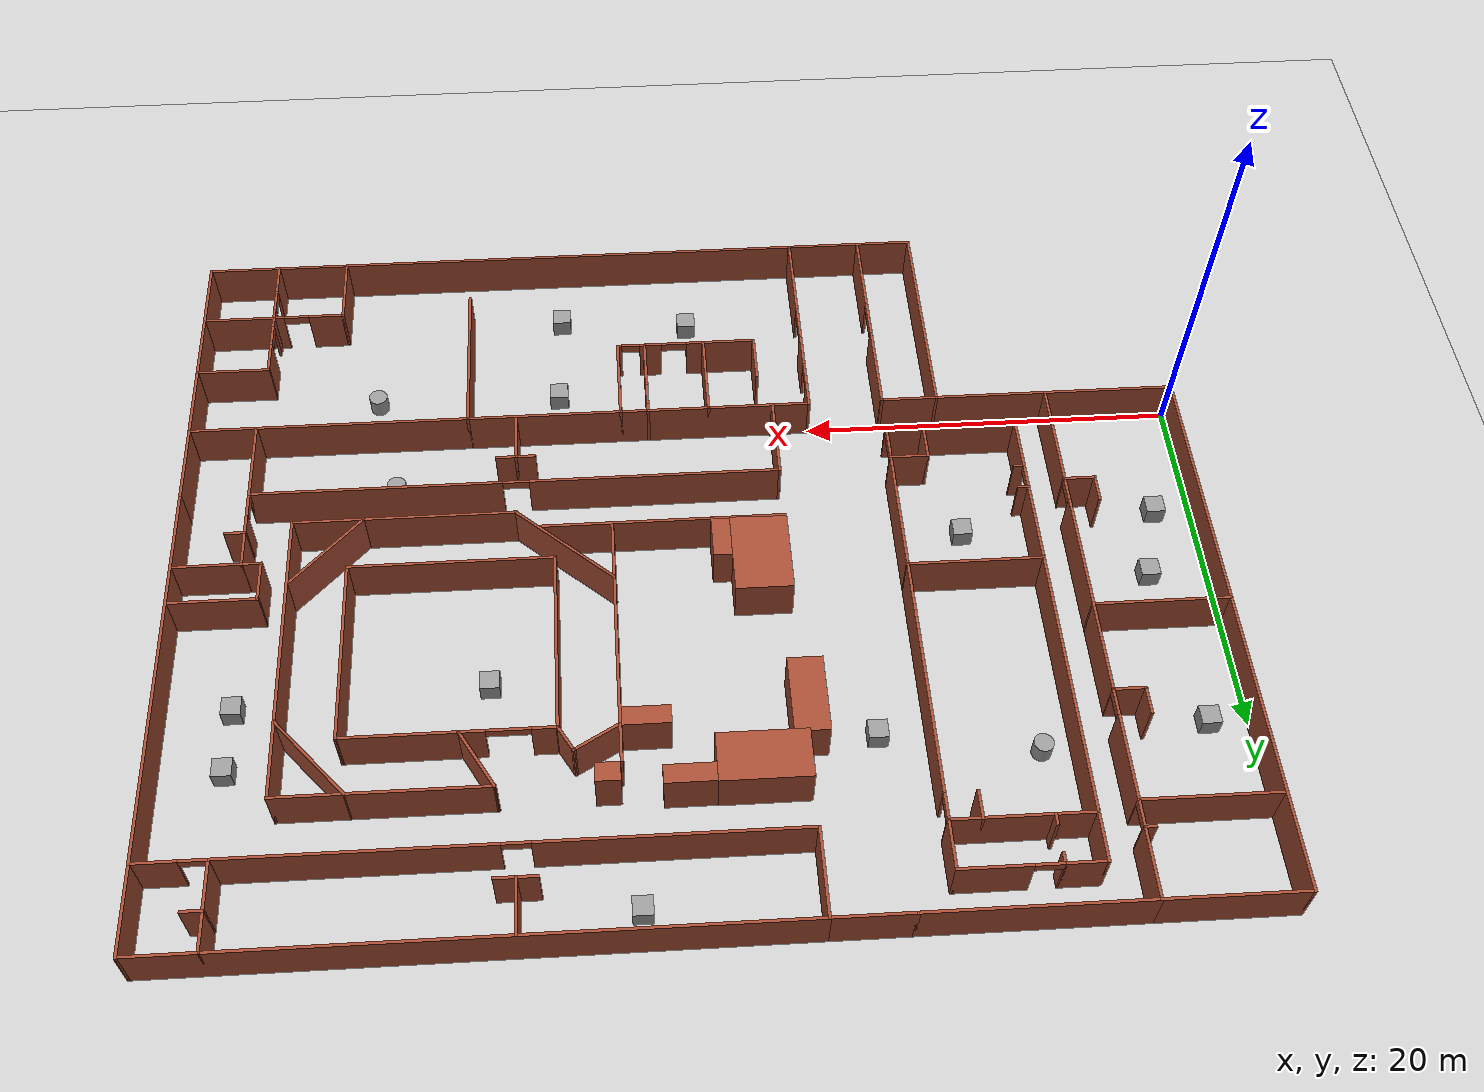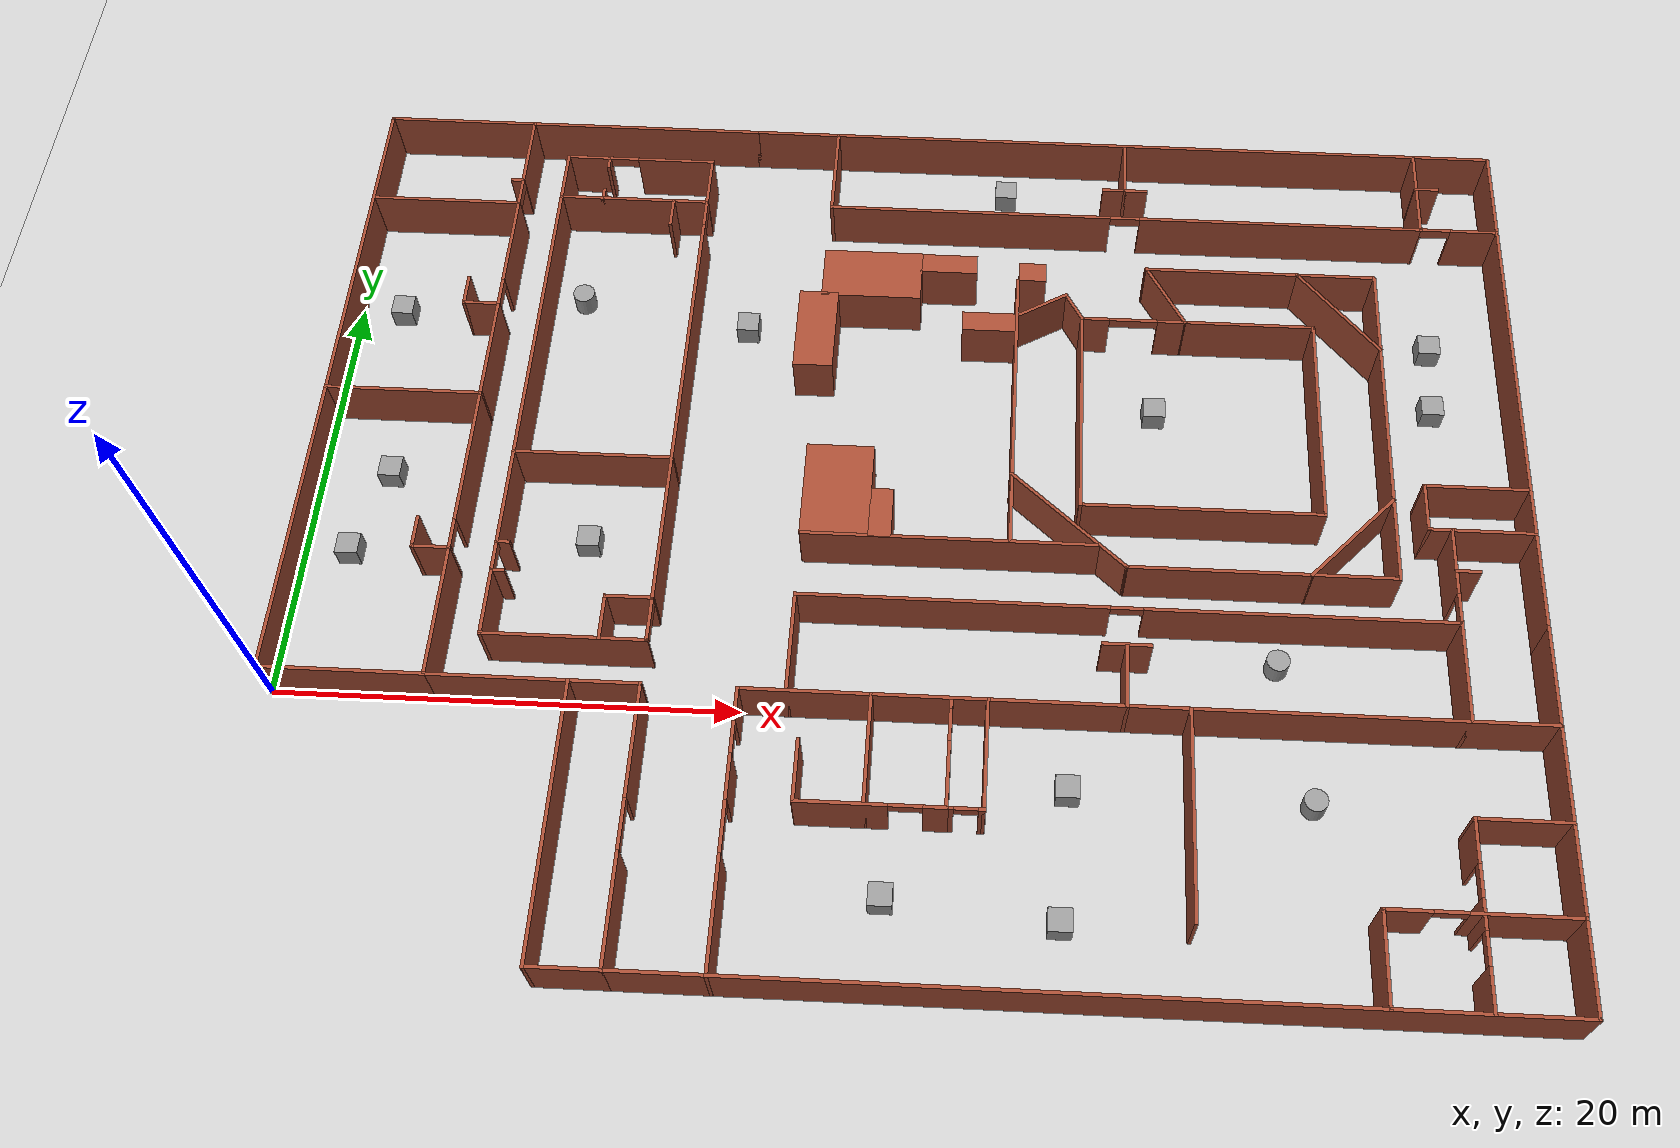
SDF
<sdf version="1.7">
 <world name="default">
  <light name="sun" type="directional">
   <pose>0 0 10 0 -0 0</pose>
   <diffuse>0.8 0.8 0.8 1</diffuse>
   <specular>0.2 0.2 0.2 1</specular>
   <attenuation>
    <range>1000</range>
    <constant>0.9</constant>
    <linear>0.01</linear>
    <quadratic>0.001</quadratic>
   </attenuation>
   <direction>-0.5 0.1 -0.9</direction>
   <spot><inner_angle>0</inner_angle><outer_angle>0</outer_angle><falloff>0</falloff></spot>
  </light>
  <model name="ground_plane">
   <static>1</static>
   <link name="link">
    <collision name="collision">
     <geometry><plane><normal>0 0 1</normal><size>100 100</size></plane></geometry>
     <surface><friction><ode><mu>100</mu><mu2>50</mu2></ode></friction></surface>
    </collision>
    <visual name="visual">
     <cast_shadows>0</cast_shadows>
     <geometry><plane><normal>0 0 1</normal><size>100 100</size></plane></geometry>
     <material>
      <script><uri>file://media/materials/scripts/gazebo.material</uri><name>Gazebo/Grey</name></script>
     </material>
    </visual>
   </link>
  </model>
  <gravity>0 0 -9.8</gravity>
  <magnetic_field>6e-06 2.3e-05 -4.2e-05</magnetic_field>
  <atmosphere type="adiabatic"/>
  <physics type="ode">
   <max_step_size>0.001</max_step_size>
   <real_time_factor>1</real_time_factor>
   <real_time_update_rate>1000</real_time_update_rate>
  </physics>
  <scene><ambient>0.4 0.4 0.4 1</ambient><background>0.7 0.7 0.7 1</background><shadows>1</shadows></scene>
  <spherical_coordinates>
   <surface_model>EARTH_WGS84</surface_model>
   <latitude_deg>0</latitude_deg>
   <longitude_deg>0</longitude_deg>
   <elevation>0</elevation>
   <heading_deg>0</heading_deg>
  </spherical_coordinates>
  <model name="indoor_total_5">
   <pose>26.8 9 0 0 -0 0</pose>
   <link name="Wall_10">
    <collision name="Wall_10_Collision">
     <geometry><box><size>7.15 0.15 2.5</size></box></geometry>
     <pose>0 0 1.25 0 -0 0</pose>
    </collision>
    <visual name="Wall_10_Visual">
     <pose>0 0 1.25 0 -0 0</pose>
     <geometry><box><size>7.15 0.15 2.5</size></box></geometry>
     <material>
      <script><uri>file://media/materials/scripts/gazebo.material</uri><name>Gazebo/Bricks</name></script>
      <ambient>1 1 1 1</ambient>
     </material>
     <meta><layer>0</layer></meta>
    </visual>
    <pose>-23.3 21 0 0 -0 0</pose>
   </link>
   <link name="Wall_101">
    <collision name="Wall_101_Collision">
     <geometry><box><size>2.95 0.15 2.5</size></box></geometry>
     <pose>0 0 1.25 0 -0 0</pose>
    </collision>
    <visual name="Wall_101_Visual">
     <pose>0 0 1.25 0 -0 0</pose>
     <geometry><box><size>2.95 0.15 2.5</size></box></geometry>
     <material>
      <script><uri>file://media/materials/scripts/gazebo.material</uri><name>Gazebo/Bricks</name></script>
      <ambient>1 1 1 1</ambient>
     </material>
     <meta><layer>0</layer></meta>
    </visual>
    <pose>9.2 -7.6 0 0 -0 1.5708</pose>
   </link>
   <link name="Wall_103">
    <collision name="Wall_103_Collision">
     <geometry><box><size>4.65 0.15 2.5</size></box></geometry>
     <pose>0 0 1.25 0 -0 0</pose>
    </collision>
    <visual name="Wall_103_Visual">
     <pose>0 0 1.25 0 -0 0</pose>
     <geometry><box><size>4.65 0.15 2.5</size></box></geometry>
     <material>
      <script><uri>file://media/materials/scripts/gazebo.material</uri><name>Gazebo/Bricks</name></script>
      <ambient>1 1 1 1</ambient>
     </material>
     <meta><layer>0</layer></meta>
    </visual>
    <pose>23.2 -6.75 0 0 -0 -1.5708</pose>
   </link>
   <link name="Wall_105">
    <collision name="Wall_105_Collision">
     <geometry><box><size>2.85 1 2.5</size></box></geometry>
     <pose>0 0 1.25 0 -0 0</pose>
    </collision>
    <visual name="Wall_105_Visual">
     <pose>0 0 1.25 0 -0 0</pose>
     <geometry><box><size>2.85 1 2.5</size></box></geometry>
     <material>
      <script><uri>file://media/materials/scripts/gazebo.material</uri><name>Gazebo/Bricks</name></script>
      <ambient>1 1 1 1</ambient>
     </material>
     <meta><layer>0</layer></meta>
    </visual>
    <pose>0.854767 13.3411 0 0 -0 0</pose>
   </link>
   <link name="Wall_107">
    <collision name="Wall_107_Collision">
     <geometry><box><size>16.15 0.15 2.5</size></box></geometry>
     <pose>0 0 1.25 0 -0 0</pose>
    </collision>
    <visual name="Wall_107_Visual">
     <pose>0 0 1.25 0 -0 0</pose>
     <geometry><box><size>16.15 0.15 2.5</size></box></geometry>
     <material>
      <script><uri>file://media/materials/scripts/gazebo.material</uri><name>Gazebo/Bricks</name></script>
      <ambient>1 1 1 1</ambient>
     </material>
     <meta><layer>0</layer></meta>
    </visual>
    <pose>20.8 5.5 0 0 -0 -1.5708</pose>
   </link>
   <link name="Wall_108">
    <collision name="Wall_108_Collision">
     <geometry><box><size>11.75 0.15 2.5</size></box></geometry>
     <pose>0 0 1.25 0 -0 0</pose>
    </collision>
    <visual name="Wall_108_Visual">
     <pose>0 0 1.25 0 -0 0</pose>
     <geometry><box><size>11.75 0.15 2.5</size></box></geometry>
     <material>
      <script><uri>file://media/materials/scripts/gazebo.material</uri><name>Gazebo/Bricks</name></script>
      <ambient>1 1 1 1</ambient>
     </material>
     <meta><layer>0</layer></meta>
    </visual>
    <pose>15 -2.5 0 0 -0 3.14159</pose>
   </link>
   <link name="Wall_11">
    <pose>-19.8 6 0 0 -0 -1.5708</pose>
    <visual name="Wall_11_Visual_0">
     <pose>-13.2375 0 1.25 0 -0 0</pose>
     <geometry><box><size>3.675 0.15 2.5</size></box></geometry>
     <material>
      <script><uri>file://media/materials/scripts/gazebo.material</uri><name>Gazebo/Bricks</name></script>
      <ambient>1 1 1 1</ambient>
     </material>
     <meta><layer>0</layer></meta>
    </visual>
    <collision name="Wall_11_Collision_0">
     <geometry><box><size>3.675 0.15 2.5</size></box></geometry>
     <pose>-13.2375 0 1.25 0 -0 0</pose>
    </collision>
    <visual name="Wall_11_Visual_1">
     <pose>-7.7 0 1.25 0 -0 0</pose>
     <geometry><box><size>4.6 0.15 2.5</size></box></geometry>
     <material>
      <script><uri>file://media/materials/scripts/gazebo.material</uri><name>Gazebo/Bricks</name></script>
      <ambient>1 1 1 1</ambient>
     </material>
     <meta><layer>0</layer></meta>
    </visual>
    <collision name="Wall_11_Collision_1">
     <geometry><box><size>4.6 0.15 2.5</size></box></geometry>
     <pose>-7.7 0 1.25 0 -0 0</pose>
    </collision>
    <visual name="Wall_11_Visual_2">
     <pose>1.8 0 1.25 0 -0 0</pose>
     <geometry><box><size>11.6 0.15 2.5</size></box></geometry>
     <material>
      <script><uri>file://media/materials/scripts/gazebo.material</uri><name>Gazebo/Bricks</name></script>
      <ambient>1 1 1 1</ambient>
     </material>
     <meta><layer>0</layer></meta>
    </visual>
    <collision name="Wall_11_Collision_2">
     <geometry><box><size>11.6 0.15 2.5</size></box></geometry>
     <pose>1.8 0 1.25 0 -0 0</pose>
    </collision>
    <visual name="Wall_11_Visual_3">
     <pose>12.0375 0 1.25 0 -0 0</pose>
     <geometry><box><size>6.075 0.15 2.5</size></box></geometry>
     <material>
      <script><uri>file://media/materials/scripts/gazebo.material</uri><name>Gazebo/Bricks</name></script>
      <ambient>1 1 1 1</ambient>
     </material>
     <meta><layer>0</layer></meta>
    </visual>
    <collision name="Wall_11_Collision_3">
     <geometry><box><size>6.075 0.15 2.5</size></box></geometry>
     <pose>12.0375 0 1.25 0 -0 0</pose>
    </collision>
    <visual name="Wall_11_Visual_4">
     <pose>-10.7 0 2.25 0 -0 0</pose>
     <geometry><box><size>1.4 0.15 0.5</size></box></geometry>
     <material>
      <script><uri>file://media/materials/scripts/gazebo.material</uri><name>Gazebo/Bricks</name></script>
      <ambient>1 1 1 1</ambient>
     </material>
     <meta><layer>0</layer></meta>
    </visual>
    <collision name="Wall_11_Collision_4">
     <geometry><box><size>1.4 0.15 0.5</size></box></geometry>
     <pose>-10.7 0 2.25 0 -0 0</pose>
    </collision>
    <visual name="Wall_11_Visual_5">
     <pose>-4.7 0 2.25 0 -0 0</pose>
     <geometry><box><size>1.4 0.15 0.5</size></box></geometry>
     <material>
      <script><uri>file://media/materials/scripts/gazebo.material</uri><name>Gazebo/Bricks</name></script>
      <ambient>1 1 1 1</ambient>
     </material>
     <meta><layer>0</layer></meta>
    </visual>
    <collision name="Wall_11_Collision_5">
     <geometry><box><size>1.4 0.15 0.5</size></box></geometry>
     <pose>-4.7 0 2.25 0 -0 0</pose>
    </collision>
    <visual name="Wall_11_Visual_6">
     <pose>8.3 0 2.25 0 -0 0</pose>
     <geometry><box><size>1.4 0.15 0.5</size></box></geometry>
     <material>
      <script><uri>file://media/materials/scripts/gazebo.material</uri><name>Gazebo/Bricks</name></script>
      <ambient>1 1 1 1</ambient>
     </material>
     <meta><layer>0</layer></meta>
    </visual>
    <collision name="Wall_11_Collision_6">
     <geometry><box><size>1.4 0.15 0.5</size></box></geometry>
     <pose>8.3 0 2.25 0 -0 0</pose>
    </collision>
   </link>
   <link name="Wall_110">
    <collision name="Wall_110_Collision">
     <geometry><box><size>6.81033 0.15 2.5</size></box></geometry>
     <pose>0 0 1.25 0 -0 0</pose>
    </collision>
    <visual name="Wall_110_Visual">
     <pose>0 0 1.25 0 -0 0</pose>
     <geometry><box><size>6.81033 0.15 2.5</size></box></geometry>
     <material>
      <script><uri>file://media/materials/scripts/gazebo.material</uri><name>Gazebo/Bricks</name></script>
      <ambient>1 1 1 1</ambient>
     </material>
     <meta><layer>0</layer></meta>
    </visual>
    <pose>6.7 -0.3 0 0 -0 -0.721655</pose>
   </link>
   <link name="Wall_112">
    <collision name="Wall_112_Collision">
     <geometry><box><size>2.42454 1 2.5</size></box></geometry>
     <pose>0 0 1.25 0 -0 0</pose>
    </collision>
    <visual name="Wall_112_Visual">
     <pose>0 0 1.25 0 -0 0</pose>
     <geometry><box><size>2.42454 1 2.5</size></box></geometry>
     <material>
      <script><uri>file://media/materials/scripts/gazebo.material</uri><name>Gazebo/Bricks</name></script>
      <ambient>1 1 1 1</ambient>
     </material>
     <meta><layer>0</layer></meta>
    </visual>
    <pose>2.9125 10.087 0 0 -0 0</pose>
   </link>
   <link name="Wall_114">
    <collision name="Wall_114_Collision">
     <geometry><box><size>12.95 0.15 2.5</size></box></geometry>
     <pose>0 0 1.25 0 -0 0</pose>
    </collision>
    <visual name="Wall_114_Visual">
     <pose>0 0 1.25 0 -0 0</pose>
     <geometry><box><size>12.95 0.15 2.5</size></box></geometry>
     <material>
      <script><uri>file://media/materials/scripts/gazebo.material</uri><name>Gazebo/Bricks</name></script>
      <ambient>1 1 1 1</ambient>
     </material>
     <meta><layer>0</layer></meta>
    </visual>
    <pose>1.6 -1.5 0 0 -0 0</pose>
   </link>
   <link name="Wall_116">
    <collision name="Wall_116_Collision">
     <geometry><box><size>4.5 3 2.5</size></box></geometry>
     <pose>0 0 1.25 0 -0 0</pose>
    </collision>
    <visual name="Wall_116_Visual">
     <pose>0 0 1.25 0 -0 0</pose>
     <geometry><box><size>4.5 3 2.5</size></box></geometry>
     <material>
      <script><uri>file://media/materials/scripts/gazebo.material</uri><name>Gazebo/Bricks</name></script>
      <ambient>1 1 1 1</ambient>
     </material>
     <meta><layer>0</layer></meta>
    </visual>
    <pose>-3.39719 0.757854 0 0 -0 1.5708</pose>
   </link>
   <link name="Wall_118">
    <collision name="Wall_118_Collision">
     <geometry><box><size>2.397 1 2.5</size></box></geometry>
     <pose>0 0 1.25 0 -0 0</pose>
    </collision>
    <visual name="Wall_118_Visual">
     <pose>0 0 1.25 0 -0 0</pose>
     <geometry><box><size>2.397 1 2.5</size></box></geometry>
     <material>
      <script><uri>file://media/materials/scripts/gazebo.material</uri><name>Gazebo/Bricks</name></script>
      <ambient>1 1 1 1</ambient>
     </material>
     <meta><layer>0</layer></meta>
    </visual>
    <pose>-1.42475 -0.340014 0 0 -0 -1.5708</pose>
   </link>
   <link name="Wall_12">
    <collision name="Wall_12_Collision">
     <geometry><box><size>7.15 0.15 2.5</size></box></geometry>
     <pose>0 0 1.25 0 -0 0</pose>
    </collision>
    <visual name="Wall_12_Visual">
     <pose>0 0 1.25 0 -0 0</pose>
     <geometry><box><size>7.15 0.15 2.5</size></box></geometry>
     <material>
      <script><uri>file://media/materials/scripts/gazebo.material</uri><name>Gazebo/Bricks</name></script>
      <ambient>1 1 1 1</ambient>
     </material>
     <meta><layer>0</layer></meta>
    </visual>
    <pose>-23.3 -9 0 0 -0 3.14159</pose>
   </link>
   <link name="Wall_120">
    <collision name="Wall_120_Collision">
     <geometry><box><size>2.74856 0.15 2.5</size></box></geometry>
     <pose>0 0 1.25 0 -0 0</pose>
    </collision>
    <visual name="Wall_120_Visual">
     <pose>0 0 1.25 0 -0 0</pose>
     <geometry><box><size>2.74856 0.15 2.5</size></box></geometry>
     <material>
      <script><uri>file://media/materials/scripts/gazebo.material</uri><name>Gazebo/Bricks</name></script>
      <ambient>1 1 1 1</ambient>
     </material>
     <meta><layer>0</layer></meta>
    </visual>
    <pose>5.325 11.15 0 0 -0 0.523919</pose>
   </link>
   <link name="Wall_121">
    <collision name="Wall_121_Collision">
     <geometry><box><size>1.65083 0.15 2.5</size></box></geometry>
     <pose>0 0 1.25 0 -0 0</pose>
    </collision>
    <visual name="Wall_121_Visual">
     <pose>0 0 1.25 0 -0 0</pose>
     <geometry><box><size>1.65083 0.15 2.5</size></box></geometry>
     <material>
      <script><uri>file://media/materials/scripts/gazebo.material</uri><name>Gazebo/Bricks</name></script>
      <ambient>1 1 1 1</ambient>
     </material>
     <meta><layer>0</layer></meta>
    </visual>
    <pose>6.825 11.15 0 0 -0 -1.04752</pose>
   </link>
   <link name="Wall_128">
    <collision name="Wall_128_Collision">
     <geometry><box><size>3.61308 0.15 2.5</size></box></geometry>
     <pose>0 0 1.25 0 -0 0</pose>
    </collision>
    <visual name="Wall_128_Visual">
     <pose>0 0 1.25 0 -0 0</pose>
     <geometry><box><size>3.61308 0.15 2.5</size></box></geometry>
     <material>
      <script><uri>file://media/materials/scripts/gazebo.material</uri><name>Gazebo/Bricks</name></script>
      <ambient>1 1 1 1</ambient>
     </material>
     <meta><layer>0</layer></meta>
    </visual>
    <pose>11.065 12 0 0 -0 -1.04771</pose>
   </link>
   <link name="Wall_130">
    <collision name="Wall_130_Collision">
     <geometry><box><size>5.53693 0.15 2.5</size></box></geometry>
     <pose>0 0 1.25 0 -0 0</pose>
    </collision>
    <visual name="Wall_130_Visual">
     <pose>0 0 1.25 0 -0 0</pose>
     <geometry><box><size>5.53693 0.15 2.5</size></box></geometry>
     <material>
      <script><uri>file://media/materials/scripts/gazebo.material</uri><name>Gazebo/Bricks</name></script>
      <ambient>1 1 1 1</ambient>
     </material>
     <meta><layer>0</layer></meta>
    </visual>
    <pose>18.9425 -0.5495 0 0 -0 0.809816</pose>
   </link>
   <link name="Wall_132">
    <collision name="Wall_132_Collision">
     <geometry><box><size>5.58972 0.15 2.5</size></box></geometry>
     <pose>0 0 1.25 0 -0 0</pose>
    </collision>
    <visual name="Wall_132_Visual">
     <pose>0 0 1.25 0 -0 0</pose>
     <geometry><box><size>5.58972 0.15 2.5</size></box></geometry>
     <material>
      <script><uri>file://media/materials/scripts/gazebo.material</uri><name>Gazebo/Bricks</name></script>
      <ambient>1 1 1 1</ambient>
     </material>
     <meta><layer>0</layer></meta>
    </visual>
    <pose>19.0085 11.4535 0 0 -0 -0.851742</pose>
   </link>
   <link name="Wall_14">
    <collision name="Wall_14_Collision">
     <geometry><box><size>7.15 0.15 2.5</size></box></geometry>
     <pose>0 0 1.25 0 -0 0</pose>
    </collision>
    <visual name="Wall_14_Visual">
     <pose>0 0 1.25 0 -0 0</pose>
     <geometry><box><size>7.15 0.15 2.5</size></box></geometry>
     <material>
      <script><uri>file://media/materials/scripts/gazebo.material</uri><name>Gazebo/Bricks</name></script>
      <ambient>1 1 1 1</ambient>
     </material>
     <meta><layer>0</layer></meta>
    </visual>
    <pose>-23.3 5 0 0 -0 0</pose>
   </link>
   <link name="Wall_142">
    <pose>12.5 10.5 0 0 -0 0</pose>
    <visual name="Wall_142_Visual_0">
     <pose>-4.705 0 1.25 0 -0 0</pose>
     <geometry><box><size>1.34 0.15 2.5</size></box></geometry>
     <material>
      <script><uri>file://media/materials/scripts/gazebo.material</uri><name>Gazebo/Bricks</name></script>
      <ambient>1 1 1 1</ambient>
     </material>
     <meta><layer>0</layer></meta>
    </visual>
    <collision name="Wall_142_Collision_0">
     <geometry><box><size>1.34 0.15 2.5</size></box></geometry>
     <pose>-4.705 0 1.25 0 -0 0</pose>
    </collision>
    <visual name="Wall_142_Visual_1">
     <pose>1.77 0 1.25 0 -0 0</pose>
     <geometry><box><size>7.21 0.15 2.5</size></box></geometry>
     <material>
      <script><uri>file://media/materials/scripts/gazebo.material</uri><name>Gazebo/Bricks</name></script>
      <ambient>1 1 1 1</ambient>
     </material>
     <meta><layer>0</layer></meta>
    </visual>
    <collision name="Wall_142_Collision_1">
     <geometry><box><size>7.21 0.15 2.5</size></box></geometry>
     <pose>1.77 0 1.25 0 -0 0</pose>
    </collision>
    <visual name="Wall_142_Visual_2">
     <pose>-2.935 0 2.25 0 -0 0</pose>
     <geometry><box><size>2.2 0.15 0.5</size></box></geometry>
     <material>
      <script><uri>file://media/materials/scripts/gazebo.material</uri><name>Gazebo/Bricks</name></script>
      <ambient>1 1 1 1</ambient>
     </material>
     <meta><layer>0</layer></meta>
    </visual>
    <collision name="Wall_142_Collision_2">
     <geometry><box><size>2.2 0.15 0.5</size></box></geometry>
     <pose>-2.935 0 2.25 0 -0 0</pose>
    </collision>
   </link>
   <link name="Wall_143">
    <collision name="Wall_143_Collision">
     <geometry><box><size>10.15 0.15 2.5</size></box></geometry>
     <pose>0 0 1.25 0 -0 0</pose>
    </collision>
    <visual name="Wall_143_Visual">
     <pose>0 0 1.25 0 -0 0</pose>
     <geometry><box><size>10.15 0.15 2.5</size></box></geometry>
     <material>
      <script><uri>file://media/materials/scripts/gazebo.material</uri><name>Gazebo/Bricks</name></script>
      <ambient>1 1 1 1</ambient>
     </material>
     <meta><layer>0</layer></meta>
    </visual>
    <pose>17.8 5.5 0 0 -0 -1.5708</pose>
   </link>
   <link name="Wall_144">
    <collision name="Wall_144_Collision">
     <geometry><box><size>10.75 0.15 2.5</size></box></geometry>
     <pose>0 0 1.25 0 -0 0</pose>
    </collision>
    <visual name="Wall_144_Visual">
     <pose>0 0 1.25 0 -0 0</pose>
     <geometry><box><size>10.75 0.15 2.5</size></box></geometry>
     <material>
      <script><uri>file://media/materials/scripts/gazebo.material</uri><name>Gazebo/Bricks</name></script>
      <ambient>1 1 1 1</ambient>
     </material>
     <meta><layer>0</layer></meta>
    </visual>
    <pose>12.5 0.5 0 0 -0 3.14159</pose>
   </link>
   <link name="Wall_145">
    <collision name="Wall_145_Collision">
     <geometry><box><size>10.15 0.15 2.5</size></box></geometry>
     <pose>0 0 1.25 0 -0 0</pose>
    </collision>
    <visual name="Wall_145_Visual">
     <pose>0 0 1.25 0 -0 0</pose>
     <geometry><box><size>10.15 0.15 2.5</size></box></geometry>
     <material>
      <script><uri>file://media/materials/scripts/gazebo.material</uri><name>Gazebo/Bricks</name></script>
      <ambient>1 1 1 1</ambient>
     </material>
     <meta><layer>0</layer></meta>
    </visual>
    <pose>7.2 5.5 0 0 -0 1.5708</pose>
   </link>
   <link name="Wall_147">
    <collision name="Wall_147_Collision">
     <geometry><box><size>2.15 0.15 2.5</size></box></geometry>
     <pose>0 0 1.25 0 -0 0</pose>
    </collision>
    <visual name="Wall_147_Visual">
     <pose>0 0 1.25 0 -0 0</pose>
     <geometry><box><size>2.15 0.15 2.5</size></box></geometry>
     <material>
      <script><uri>file://media/materials/scripts/gazebo.material</uri><name>Gazebo/Bricks</name></script>
      <ambient>1 1 1 1</ambient>
     </material>
     <meta><layer>0</layer></meta>
    </visual>
    <pose>9.2 18.2 0 0 -0 0</pose>
   </link>
   <link name="Wall_149">
    <collision name="Wall_149_Collision">
     <geometry><box><size>1.15 0.15 2.5</size></box></geometry>
     <pose>0 0 1.25 0 -0 0</pose>
    </collision>
    <visual name="Wall_149_Visual">
     <pose>0 0 1.25 0 -0 0</pose>
     <geometry><box><size>1.15 0.15 2.5</size></box></geometry>
     <material>
      <script><uri>file://media/materials/scripts/gazebo.material</uri><name>Gazebo/Bricks</name></script>
      <ambient>1 1 1 1</ambient>
     </material>
     <meta><layer>0</layer></meta>
    </visual>
    <pose>23.7 19 0 0 -0 0</pose>
   </link>
   <link name="Wall_151">
    <collision name="Wall_151_Collision">
     <geometry><box><size>1.15 0.15 2.5</size></box></geometry>
     <pose>0 0 1.25 0 -0 0</pose>
    </collision>
    <visual name="Wall_151_Visual">
     <pose>0 0 1.25 0 -0 0</pose>
     <geometry><box><size>1.15 0.15 2.5</size></box></geometry>
     <material>
      <script><uri>file://media/materials/scripts/gazebo.material</uri><name>Gazebo/Bricks</name></script>
      <ambient>1 1 1 1</ambient>
     </material>
     <meta><layer>0</layer></meta>
    </visual>
    <pose>23.7 -2 0 0 -0 0</pose>
   </link>
   <link name="Wall_153">
    <collision name="Wall_153_Collision">
     <geometry><box><size>2.78298 0.15 2.5</size></box></geometry>
     <pose>0 0 1.25 0 -0 0</pose>
    </collision>
    <visual name="Wall_153_Visual">
     <pose>0 0 1.25 0 -0 0</pose>
     <geometry><box><size>2.78298 0.15 2.5</size></box></geometry>
     <material>
      <script><uri>file://media/materials/scripts/gazebo.material</uri><name>Gazebo/Bricks</name></script>
      <ambient>1 1 1 1</ambient>
     </material>
     <meta><layer>0</layer></meta>
    </visual>
    <pose>-4.12125 -12.4835 0 0 -0 -1.57061</pose>
   </link>
   <link name="Wall_156">
    <collision name="Wall_156_Collision">
     <geometry><box><size>4.95 0.15 2.5</size></box></geometry>
     <pose>0 0 1.25 0 -0 0</pose>
    </collision>
    <visual name="Wall_156_Visual">
     <pose>0 0 1.25 0 -0 0</pose>
     <geometry><box><size>4.95 0.15 2.5</size></box></geometry>
     <material>
      <script><uri>file://media/materials/scripts/gazebo.material</uri><name>Gazebo/Bricks</name></script>
      <ambient>1 1 1 1</ambient>
     </material>
     <meta><layer>0</layer></meta>
    </visual>
    <pose>-1.3 -11.4 0 0 -0 1.5708</pose>
   </link>
   <link name="Wall_158">
    <pose>2 -11.4 0 0 -0 -1.5708</pose>
    <visual name="Wall_158_Visual_0">
     <pose>-2.19297 0 1.25 0 -0 0</pose>
     <geometry><box><size>0.564066 0.15 2.5</size></box></geometry>
     <material>
      <script><uri>file://media/materials/scripts/gazebo.material</uri><name>Gazebo/Bricks</name></script>
      <ambient>1 1 1 1</ambient>
     </material>
     <meta><layer>0</layer></meta>
    </visual>
    <collision name="Wall_158_Collision_0">
     <geometry><box><size>0.564066 0.15 2.5</size></box></geometry>
     <pose>-2.19297 0 1.25 0 -0 0</pose>
    </collision>
    <visual name="Wall_158_Visual_1">
     <pose>0.982033 0 1.25 0 -0 0</pose>
     <geometry><box><size>2.98593 0.15 2.5</size></box></geometry>
     <material>
      <script><uri>file://media/materials/scripts/gazebo.material</uri><name>Gazebo/Bricks</name></script>
      <ambient>1 1 1 1</ambient>
     </material>
     <meta><layer>0</layer></meta>
    </visual>
    <collision name="Wall_158_Collision_1">
     <geometry><box><size>2.98593 0.15 2.5</size></box></geometry>
     <pose>0.982033 0 1.25 0 -0 0</pose>
    </collision>
    <visual name="Wall_158_Visual_2">
     <pose>-1.21093 0 2.25 0 -0 0</pose>
     <geometry><box><size>1.4 0.15 0.5</size></box></geometry>
     <material>
      <script><uri>file://media/materials/scripts/gazebo.material</uri><name>Gazebo/Bricks</name></script>
      <ambient>1 1 1 1</ambient>
     </material>
     <meta><layer>0</layer></meta>
    </visual>
    <collision name="Wall_158_Collision_2">
     <geometry><box><size>1.4 0.15 0.5</size></box></geometry>
     <pose>-1.21093 0 2.25 0 -0 0</pose>
    </collision>
   </link>
   <link name="Wall_159">
    <pose>2.75 -13.8 0 0 -0 0</pose>
    <visual name="Wall_159_Visual_0">
     <pose>-0.651036 0 1.25 0 -0 0</pose>
     <geometry><box><size>0.347928 0.15 2.5</size></box></geometry>
     <material>
      <script><uri>file://media/materials/scripts/gazebo.material</uri><name>Gazebo/Bricks</name></script>
      <ambient>1 1 1 1</ambient>
     </material>
     <meta><layer>0</layer></meta>
    </visual>
    <collision name="Wall_159_Collision_0">
     <geometry><box><size>0.347928 0.15 2.5</size></box></geometry>
     <pose>-0.651036 0 1.25 0 -0 0</pose>
    </collision>
    <visual name="Wall_159_Visual_1">
     <pose>0.673964 0 1.25 0 -0 0</pose>
     <geometry><box><size>0.302072 0.15 2.5</size></box></geometry>
     <material>
      <script><uri>file://media/materials/scripts/gazebo.material</uri><name>Gazebo/Bricks</name></script>
      <ambient>1 1 1 1</ambient>
     </material>
     <meta><layer>0</layer></meta>
    </visual>
    <collision name="Wall_159_Collision_1">
     <geometry><box><size>0.302072 0.15 2.5</size></box></geometry>
     <pose>0.673964 0 1.25 0 -0 0</pose>
    </collision>
    <visual name="Wall_159_Visual_2">
     <pose>0.022928 0 2.25 0 -0 0</pose>
     <geometry><box><size>1 0.15 0.5</size></box></geometry>
     <material>
      <script><uri>file://media/materials/scripts/gazebo.material</uri><name>Gazebo/Bricks</name></script>
      <ambient>1 1 1 1</ambient>
     </material>
     <meta><layer>0</layer></meta>
    </visual>
    <collision name="Wall_159_Collision_2">
     <geometry><box><size>1 0.15 0.5</size></box></geometry>
     <pose>0.022928 0 2.25 0 -0 0</pose>
    </collision>
   </link>
   <link name="Wall_16">
    <collision name="Wall_16_Collision">
     <geometry><box><size>7.15 0.15 2.5</size></box></geometry>
     <pose>0 0 1.25 0 -0 0</pose>
    </collision>
    <visual name="Wall_16_Visual">
     <pose>0 0 1.25 0 -0 0</pose>
     <geometry><box><size>7.15 0.15 2.5</size></box></geometry>
     <material>
      <script><uri>file://media/materials/scripts/gazebo.material</uri><name>Gazebo/Bricks</name></script>
      <ambient>1 1 1 1</ambient>
     </material>
     <meta><layer>0</layer></meta>
    </visual>
    <pose>-23.3 16 0 0 -0 0</pose>
   </link>
   <link name="Wall_160">
    <collision name="Wall_160_Collision">
     <geometry><box><size>4.95 0.15 2.5</size></box></geometry>
     <pose>0 0 1.25 0 -0 0</pose>
    </collision>
    <visual name="Wall_160_Visual">
     <pose>0 0 1.25 0 -0 0</pose>
     <geometry><box><size>4.95 0.15 2.5</size></box></geometry>
     <material>
      <script><uri>file://media/materials/scripts/gazebo.material</uri><name>Gazebo/Bricks</name></script>
      <ambient>1 1 1 1</ambient>
     </material>
     <meta><layer>0</layer></meta>
    </visual>
    <pose>3.5 -11.4 0 0 -0 1.5708</pose>
   </link>
   <link name="Wall_162">
    <collision name="Wall_162_Collision">
     <geometry><box><size>4.05 0.15 2.5</size></box></geometry>
     <pose>0 0 1.25 0 -0 0</pose>
    </collision>
    <visual name="Wall_162_Visual">
     <pose>0 0 1.25 0 -0 0</pose>
     <geometry><box><size>4.05 0.15 2.5</size></box></geometry>
     <material>
      <script><uri>file://media/materials/scripts/gazebo.material</uri><name>Gazebo/Bricks</name></script>
      <ambient>1 1 1 1</ambient>
     </material>
     <meta><layer>0</layer></meta>
    </visual>
    <pose>19 -19.05 0 0 -0 1.5708</pose>
   </link>
   <link name="Wall_163">
    <pose>22.9 -17.1 0 0 -0 0</pose>
    <visual name="Wall_163_Visual_0">
     <pose>-2.97254 0 1.25 0 -0 0</pose>
     <geometry><box><size>2.00492 0.15 2.5</size></box></geometry>
     <material>
      <script><uri>file://media/materials/scripts/gazebo.material</uri><name>Gazebo/Bricks</name></script>
      <ambient>1 1 1 1</ambient>
     </material>
     <meta><layer>0</layer></meta>
    </visual>
    <collision name="Wall_163_Collision_0">
     <geometry><box><size>2.00492 0.15 2.5</size></box></geometry>
     <pose>-2.97254 0 1.25 0 -0 0</pose>
    </collision>
    <visual name="Wall_163_Visual_1">
     <pose>1.70246 0 1.25 0 -0 0</pose>
     <geometry><box><size>4.54508 0.15 2.5</size></box></geometry>
     <material>
      <script><uri>file://media/materials/scripts/gazebo.material</uri><name>Gazebo/Bricks</name></script>
      <ambient>1 1 1 1</ambient>
     </material>
     <meta><layer>0</layer></meta>
    </visual>
    <collision name="Wall_163_Collision_1">
     <geometry><box><size>4.54508 0.15 2.5</size></box></geometry>
     <pose>1.70246 0 1.25 0 -0 0</pose>
    </collision>
    <visual name="Wall_163_Visual_2">
     <pose>-1.27008 0 2.25 0 -0 0</pose>
     <geometry><box><size>1.4 0.15 0.5</size></box></geometry>
     <material>
      <script><uri>file://media/materials/scripts/gazebo.material</uri><name>Gazebo/Bricks</name></script>
      <ambient>1 1 1 1</ambient>
     </material>
     <meta><layer>0</layer></meta>
    </visual>
    <collision name="Wall_163_Collision_2">
     <geometry><box><size>1.4 0.15 0.5</size></box></geometry>
     <pose>-1.27008 0 2.25 0 -0 0</pose>
    </collision>
   </link>
   <link name="Wall_165">
    <collision name="Wall_165_Collision">
     <geometry><box><size>4.05 0.15 2.5</size></box></geometry>
     <pose>0 0 1.25 0 -0 0</pose>
    </collision>
    <visual name="Wall_165_Visual">
     <pose>0 0 1.25 0 -0 0</pose>
     <geometry><box><size>4.05 0.15 2.5</size></box></geometry>
     <material>
      <script><uri>file://media/materials/scripts/gazebo.material</uri><name>Gazebo/Bricks</name></script>
      <ambient>1 1 1 1</ambient>
     </material>
     <meta><layer>0</layer></meta>
    </visual>
    <pose>24.85 -13.2 0 0 -0 3.14159</pose>
   </link>
   <link name="Wall_166">
    <pose>22.9 -17.1 0 0 -0 -1.5708</pose>
    <visual name="Wall_166_Visual_0">
     <pose>-3.00683 0 1.25 0 -0 0</pose>
     <geometry><box><size>1.93633 0.15 2.5</size></box></geometry>
     <material>
      <script><uri>file://media/materials/scripts/gazebo.material</uri><name>Gazebo/Bricks</name></script>
      <ambient>1 1 1 1</ambient>
     </material>
     <meta><layer>0</layer></meta>
    </visual>
    <collision name="Wall_166_Collision_0">
     <geometry><box><size>1.93633 0.15 2.5</size></box></geometry>
     <pose>-3.00683 0 1.25 0 -0 0</pose>
    </collision>
    <visual name="Wall_166_Visual_1">
     <pose>0.014946 0 1.25 0 -0 0</pose>
     <geometry><box><size>1.30723 0.15 2.5</size></box></geometry>
     <material>
      <script><uri>file://media/materials/scripts/gazebo.material</uri><name>Gazebo/Bricks</name></script>
      <ambient>1 1 1 1</ambient>
     </material>
     <meta><layer>0</layer></meta>
    </visual>
    <collision name="Wall_166_Collision_1">
     <geometry><box><size>1.30723 0.15 2.5</size></box></geometry>
     <pose>0.014946 0 1.25 0 -0 0</pose>
    </collision>
    <visual name="Wall_166_Visual_2">
     <pose>3.02178 0 1.25 0 -0 0</pose>
     <geometry><box><size>1.90644 0.15 2.5</size></box></geometry>
     <material>
      <script><uri>file://media/materials/scripts/gazebo.material</uri><name>Gazebo/Bricks</name></script>
      <ambient>1 1 1 1</ambient>
     </material>
     <meta><layer>0</layer></meta>
    </visual>
    <collision name="Wall_166_Collision_2">
     <geometry><box><size>1.90644 0.15 2.5</size></box></geometry>
     <pose>3.02178 0 1.25 0 -0 0</pose>
    </collision>
    <visual name="Wall_166_Visual_3">
     <pose>-1.33867 0 2.25 0 -0 0</pose>
     <geometry><box><size>1.4 0.15 0.5</size></box></geometry>
     <material>
      <script><uri>file://media/materials/scripts/gazebo.material</uri><name>Gazebo/Bricks</name></script>
      <ambient>1 1 1 1</ambient>
     </material>
     <meta><layer>0</layer></meta>
    </visual>
    <collision name="Wall_166_Collision_3">
     <geometry><box><size>1.4 0.15 0.5</size></box></geometry>
     <pose>-1.33867 0 2.25 0 -0 0</pose>
    </collision>
    <visual name="Wall_166_Visual_4">
     <pose>1.36856 0 2.25 0 -0 0</pose>
     <geometry><box><size>1.4 0.15 0.5</size></box></geometry>
     <material>
      <script><uri>file://media/materials/scripts/gazebo.material</uri><name>Gazebo/Bricks</name></script>
      <ambient>1 1 1 1</ambient>
     </material>
     <meta><layer>0</layer></meta>
    </visual>
    <collision name="Wall_166_Collision_4">
     <geometry><box><size>1.4 0.15 0.5</size></box></geometry>
     <pose>1.36856 0 2.25 0 -0 0</pose>
    </collision>
   </link>
   <link name="Wall_168">
    <collision name="Wall_168_Collision">
     <geometry><box><size>2.15 0.15 2.5</size></box></geometry>
     <pose>0 0 1.25 0 -0 0</pose>
    </collision>
    <visual name="Wall_168_Visual">
     <pose>0 0 1.25 0 -0 0</pose>
     <geometry><box><size>2.15 0.15 2.5</size></box></geometry>
     <material>
      <script><uri>file://media/materials/scripts/gazebo.material</uri><name>Gazebo/Bricks</name></script>
      <ambient>1 1 1 1</ambient>
     </material>
     <meta><layer>0</layer></meta>
    </visual>
    <pose>9.2 -6.2 0 0 -0 0</pose>
   </link>
   <link name="Wall_174">
    <collision name="Wall_174_Collision">
     <geometry><box><size>1.25 1 2.5</size></box></geometry>
     <pose>0 0 1.25 0 -0 0</pose>
    </collision>
    <visual name="Wall_174_Visual">
     <pose>0 0 1.25 0 -0 0</pose>
     <geometry><box><size>1.25 1 2.5</size></box></geometry>
     <material>
      <script><uri>file://media/materials/scripts/gazebo.material</uri><name>Gazebo/Bricks</name></script>
      <ambient>1 1 1 1</ambient>
     </material>
     <meta><layer>0</layer></meta>
    </visual>
    <pose>4.88086 13.0421 0 0 -0 0</pose>
   </link>
   <link name="Wall_176">
    <collision name="Wall_176_Collision">
     <geometry><box><size>4.65 0.15 2.5</size></box></geometry>
     <pose>0 0 1.25 0 -0 0</pose>
    </collision>
    <visual name="Wall_176_Visual">
     <pose>0 0 1.25 0 -0 0</pose>
     <geometry><box><size>4.65 0.15 2.5</size></box></geometry>
     <material>
      <script><uri>file://media/materials/scripts/gazebo.material</uri><name>Gazebo/Bricks</name></script>
      <ambient>1 1 1 1</ambient>
     </material>
     <meta><layer>0</layer></meta>
    </visual>
    <pose>26.8 -6.75 0 0 -0 -1.5708</pose>
   </link>
   <link name="Wall_18">
    <collision name="Wall_18_Collision">
     <geometry><box><size>0.65 0.15 2.5</size></box></geometry>
     <pose>0 0 1.25 0 -0 0</pose>
    </collision>
    <visual name="Wall_18_Visual">
     <pose>0 0 1.25 0 -0 0</pose>
     <geometry><box><size>0.65 0.15 2.5</size></box></geometry>
     <material>
      <script><uri>file://media/materials/scripts/gazebo.material</uri><name>Gazebo/Bricks</name></script>
      <ambient>1 1 1 1</ambient>
     </material>
     <meta><layer>0</layer></meta>
    </visual>
    <pose>-20.05 17.4 0 0 -0 0</pose>
   </link>
   <link name="Wall_180">
    <pose>-1.0605 -13.8 0 0 -0 0</pose>
    <visual name="Wall_180_Visual_0">
     <pose>-1.20375 0 1.25 0 -0 0</pose>
     <geometry><box><size>3.86349 0.15 2.5</size></box></geometry>
     <material>
      <script><uri>file://media/materials/scripts/gazebo.material</uri><name>Gazebo/Bricks</name></script>
      <ambient>1 1 1 1</ambient>
     </material>
     <meta><layer>0</layer></meta>
    </visual>
    <collision name="Wall_180_Collision_0">
     <geometry><box><size>3.86349 0.15 2.5</size></box></geometry>
     <pose>-1.20375 0 1.25 0 -0 0</pose>
    </collision>
    <visual name="Wall_180_Visual_1">
     <pose>2.63175 0 1.25 0 -0 0</pose>
     <geometry><box><size>1.00751 0.15 2.5</size></box></geometry>
     <material>
      <script><uri>file://media/materials/scripts/gazebo.material</uri><name>Gazebo/Bricks</name></script>
      <ambient>1 1 1 1</ambient>
     </material>
     <meta><layer>0</layer></meta>
    </visual>
    <collision name="Wall_180_Collision_1">
     <geometry><box><size>1.00751 0.15 2.5</size></box></geometry>
     <pose>2.63175 0 1.25 0 -0 0</pose>
    </collision>
    <visual name="Wall_180_Visual_2">
     <pose>1.42799 0 2.25 0 -0 0</pose>
     <geometry><box><size>1.4 0.15 0.5</size></box></geometry>
     <material>
      <script><uri>file://media/materials/scripts/gazebo.material</uri><name>Gazebo/Bricks</name></script>
      <ambient>1 1 1 1</ambient>
     </material>
     <meta><layer>0</layer></meta>
    </visual>
    <collision name="Wall_180_Collision_2">
     <geometry><box><size>1.4 0.15 0.5</size></box></geometry>
     <pose>1.42799 0 2.25 0 -0 0</pose>
    </collision>
   </link>
   <link name="Wall_182">
    <collision name="Wall_182_Collision">
     <geometry><box><size>4.15 0.15 2.5</size></box></geometry>
     <pose>0 0 1.25 0 -0 0</pose>
    </collision>
    <visual name="Wall_182_Visual">
     <pose>0 0 1.25 0 -0 0</pose>
     <geometry><box><size>4.15 0.15 2.5</size></box></geometry>
     <material>
      <script><uri>file://media/materials/scripts/gazebo.material</uri><name>Gazebo/Bricks</name></script>
      <ambient>1 1 1 1</ambient>
     </material>
     <meta><layer>0</layer></meta>
    </visual>
    <pose>-6.8 21 0 0 -0 0</pose>
   </link>
   <link name="Wall_184">
    <collision name="Wall_184_Collision">
     <geometry><box><size>4.15 0.15 2.5</size></box></geometry>
     <pose>0 0 1.25 0 -0 0</pose>
    </collision>
    <visual name="Wall_184_Visual">
     <pose>0 0 1.25 0 -0 0</pose>
     <geometry><box><size>4.15 0.15 2.5</size></box></geometry>
     <material>
      <script><uri>file://media/materials/scripts/gazebo.material</uri><name>Gazebo/Bricks</name></script>
      <ambient>1 1 1 1</ambient>
     </material>
     <meta><layer>0</layer></meta>
    </visual>
    <pose>-8.8 -21 0 0 -0 0</pose>
   </link>
   <link name="Wall_20">
    <collision name="Wall_20_Collision">
     <geometry><box><size>11.15 0.15 2.5</size></box></geometry>
     <pose>0 0 1.25 0 -0 0</pose>
    </collision>
    <visual name="Wall_20_Visual">
     <pose>0 0 1.25 0 -0 0</pose>
     <geometry><box><size>11.15 0.15 2.5</size></box></geometry>
     <material>
      <script><uri>file://media/materials/scripts/gazebo.material</uri><name>Gazebo/Bricks</name></script>
      <ambient>1 1 1 1</ambient>
     </material>
     <meta><layer>0</layer></meta>
    </visual>
    <pose>-14.3 21 0 0 -0 0</pose>
   </link>
   <link name="Wall_22">
    <pose>-14.3 19 0 0 -0 0</pose>
    <visual name="Wall_22_Visual_0">
     <pose>-2.5375 0 1.25 0 -0 0</pose>
     <geometry><box><size>2.075 0.15 2.5</size></box></geometry>
     <material>
      <script><uri>file://media/materials/scripts/gazebo.material</uri><name>Gazebo/Bricks</name></script>
      <ambient>1 1 1 1</ambient>
     </material>
     <meta><layer>0</layer></meta>
    </visual>
    <collision name="Wall_22_Collision_0">
     <geometry><box><size>2.075 0.15 2.5</size></box></geometry>
     <pose>-2.5375 0 1.25 0 -0 0</pose>
    </collision>
    <visual name="Wall_22_Visual_1">
     <pose>1.7375 0 1.25 0 -0 0</pose>
     <geometry><box><size>3.675 0.15 2.5</size></box></geometry>
     <material>
      <script><uri>file://media/materials/scripts/gazebo.material</uri><name>Gazebo/Bricks</name></script>
      <ambient>1 1 1 1</ambient>
     </material>
     <meta><layer>0</layer></meta>
    </visual>
    <collision name="Wall_22_Collision_1">
     <geometry><box><size>3.675 0.15 2.5</size></box></geometry>
     <pose>1.7375 0 1.25 0 -0 0</pose>
    </collision>
    <visual name="Wall_22_Visual_2">
     <pose>-0.8 0 2.25 0 -0 0</pose>
     <geometry><box><size>1.4 0.15 0.5</size></box></geometry>
     <material>
      <script><uri>file://media/materials/scripts/gazebo.material</uri><name>Gazebo/Bricks</name></script>
      <ambient>1 1 1 1</ambient>
     </material>
     <meta><layer>0</layer></meta>
    </visual>
    <collision name="Wall_22_Collision_2">
     <geometry><box><size>1.4 0.15 0.5</size></box></geometry>
     <pose>-0.8 0 2.25 0 -0 0</pose>
    </collision>
   </link>
   <link name="Wall_23">
    <pose>-10.8 6 0 0 -0 -1.5708</pose>
    <visual name="Wall_23_Visual_0">
     <pose>-11.7875 0 1.25 0 -0 0</pose>
     <geometry><box><size>2.575 0.15 2.5</size></box></geometry>
     <material>
      <script><uri>file://media/materials/scripts/gazebo.material</uri><name>Gazebo/Bricks</name></script>
      <ambient>1 1 1 1</ambient>
     </material>
     <meta><layer>0</layer></meta>
    </visual>
    <collision name="Wall_23_Collision_0">
     <geometry><box><size>2.575 0.15 2.5</size></box></geometry>
     <pose>-11.7875 0 1.25 0 -0 0</pose>
    </collision>
    <visual name="Wall_23_Visual_1">
     <pose>0.95 0 1.25 0 -0 0</pose>
     <geometry><box><size>20.1 0.15 2.5</size></box></geometry>
     <material>
      <script><uri>file://media/materials/scripts/gazebo.material</uri><name>Gazebo/Bricks</name></script>
      <ambient>1 1 1 1</ambient>
     </material>
     <meta><layer>0</layer></meta>
    </visual>
    <collision name="Wall_23_Collision_1">
     <geometry><box><size>20.1 0.15 2.5</size></box></geometry>
     <pose>0.95 0 1.25 0 -0 0</pose>
    </collision>
    <visual name="Wall_23_Visual_2">
     <pose>13.0375 0 1.25 0 -0 0</pose>
     <geometry><box><size>0.075 0.15 2.5</size></box></geometry>
     <material>
      <script><uri>file://media/materials/scripts/gazebo.material</uri><name>Gazebo/Bricks</name></script>
      <ambient>1 1 1 1</ambient>
     </material>
     <meta><layer>0</layer></meta>
    </visual>
    <collision name="Wall_23_Collision_2">
     <geometry><box><size>0.075 0.15 2.5</size></box></geometry>
     <pose>13.0375 0 1.25 0 -0 0</pose>
    </collision>
    <visual name="Wall_23_Visual_3">
     <pose>-9.8 0 2.25 0 -0 0</pose>
     <geometry><box><size>1.4 0.15 0.5</size></box></geometry>
     <material>
      <script><uri>file://media/materials/scripts/gazebo.material</uri><name>Gazebo/Bricks</name></script>
      <ambient>1 1 1 1</ambient>
     </material>
     <meta><layer>0</layer></meta>
    </visual>
    <collision name="Wall_23_Collision_3">
     <geometry><box><size>1.4 0.15 0.5</size></box></geometry>
     <pose>-9.8 0 2.25 0 -0 0</pose>
    </collision>
    <visual name="Wall_23_Visual_4">
     <pose>12 0 2.25 0 -0 0</pose>
     <geometry><box><size>2 0.15 0.5</size></box></geometry>
     <material>
      <script><uri>file://media/materials/scripts/gazebo.material</uri><name>Gazebo/Bricks</name></script>
      <ambient>1 1 1 1</ambient>
     </material>
     <meta><layer>0</layer></meta>
    </visual>
    <collision name="Wall_23_Collision_4">
     <geometry><box><size>2 0.15 0.5</size></box></geometry>
     <pose>12 0 2.25 0 -0 0</pose>
    </collision>
   </link>
   <link name="Wall_24">
    <collision name="Wall_24_Collision">
     <geometry><box><size>7.15 0.15 2.5</size></box></geometry>
     <pose>0 0 1.25 0 -0 0</pose>
    </collision>
    <visual name="Wall_24_Visual">
     <pose>0 0 1.25 0 -0 0</pose>
     <geometry><box><size>7.15 0.15 2.5</size></box></geometry>
     <material>
      <script><uri>file://media/materials/scripts/gazebo.material</uri><name>Gazebo/Bricks</name></script>
      <ambient>1 1 1 1</ambient>
     </material>
     <meta><layer>0</layer></meta>
    </visual>
    <pose>-14.3 -7 0 0 -0 3.14159</pose>
   </link>
   <link name="Wall_25">
    <pose>-17.8 6 0 0 -0 1.5708</pose>
    <visual name="Wall_25_Visual_0">
     <pose>-11.5375 0 1.25 0 -0 0</pose>
     <geometry><box><size>3.075 0.15 2.5</size></box></geometry>
     <material>
      <script><uri>file://media/materials/scripts/gazebo.material</uri><name>Gazebo/Bricks</name></script>
      <ambient>1 1 1 1</ambient>
     </material>
     <meta><layer>0</layer></meta>
    </visual>
    <collision name="Wall_25_Collision_0">
     <geometry><box><size>3.075 0.15 2.5</size></box></geometry>
     <pose>-11.5375 0 1.25 0 -0 0</pose>
    </collision>
    <visual name="Wall_25_Visual_1">
     <pose>2.2375 0 1.25 0 -0 0</pose>
     <geometry><box><size>21.675 0.15 2.5</size></box></geometry>
     <material>
      <script><uri>file://media/materials/scripts/gazebo.material</uri><name>Gazebo/Bricks</name></script>
      <ambient>1 1 1 1</ambient>
     </material>
     <meta><layer>0</layer></meta>
    </visual>
    <collision name="Wall_25_Collision_1">
     <geometry><box><size>21.675 0.15 2.5</size></box></geometry>
     <pose>2.2375 0 1.25 0 -0 0</pose>
    </collision>
    <visual name="Wall_25_Visual_2">
     <pose>-9.3 0 2.25 0 -0 0</pose>
     <geometry><box><size>1.4 0.15 0.5</size></box></geometry>
     <material>
      <script><uri>file://media/materials/scripts/gazebo.material</uri><name>Gazebo/Bricks</name></script>
      <ambient>1 1 1 1</ambient>
     </material>
     <meta><layer>0</layer></meta>
    </visual>
    <collision name="Wall_25_Collision_2">
     <geometry><box><size>1.4 0.15 0.5</size></box></geometry>
     <pose>-9.3 0 2.25 0 -0 0</pose>
    </collision>
   </link>
   <link name="Wall_27">
    <collision name="Wall_27_Collision">
     <geometry><box><size>9.15 0.15 2.5</size></box></geometry>
     <pose>0 0 1.25 0 -0 0</pose>
    </collision>
    <visual name="Wall_27_Visual">
     <pose>0 0 1.25 0 -0 0</pose>
     <geometry><box><size>9.15 0.15 2.5</size></box></geometry>
     <material>
      <script><uri>file://media/materials/scripts/gazebo.material</uri><name>Gazebo/Bricks</name></script>
      <ambient>1 1 1 1</ambient>
     </material>
     <meta><layer>0</layer></meta>
    </visual>
    <pose>-15.3 -9 0 0 -0 0</pose>
   </link>
   <link name="Wall_29">
    <collision name="Wall_29_Collision">
     <geometry><box><size>12.15 0.15 2.5</size></box></geometry>
     <pose>0 0 1.25 0 -0 0</pose>
    </collision>
    <visual name="Wall_29_Visual">
     <pose>0 0 1.25 0 -0 0</pose>
     <geometry><box><size>12.15 0.15 2.5</size></box></geometry>
     <material>
      <script><uri>file://media/materials/scripts/gazebo.material</uri><name>Gazebo/Bricks</name></script>
      <ambient>1 1 1 1</ambient>
     </material>
     <meta><layer>0</layer></meta>
    </visual>
    <pose>-13.8 -15 0 0 -0 -1.5708</pose>
   </link>
   <link name="Wall_30">
    <collision name="Wall_30_Collision">
     <geometry><box><size>3.15 0.15 2.5</size></box></geometry>
     <pose>0 0 1.25 0 -0 0</pose>
    </collision>
    <visual name="Wall_30_Visual">
     <pose>0 0 1.25 0 -0 0</pose>
     <geometry><box><size>3.15 0.15 2.5</size></box></geometry>
     <material>
      <script><uri>file://media/materials/scripts/gazebo.material</uri><name>Gazebo/Bricks</name></script>
      <ambient>1 1 1 1</ambient>
     </material>
     <meta><layer>0</layer></meta>
    </visual>
    <pose>-12.3 -21 0 0 -0 0</pose>
   </link>
   <link name="Wall_31">
    <pose>-10.8 -15 0 0 -0 1.5708</pose>
    <visual name="Wall_31_Visual_0">
     <pose>-3.6375 0 1.25 0 -0 0</pose>
     <geometry><box><size>4.875 0.15 2.5</size></box></geometry>
     <material>
      <script><uri>file://media/materials/scripts/gazebo.material</uri><name>Gazebo/Bricks</name></script>
      <ambient>1 1 1 1</ambient>
     </material>
     <meta><layer>0</layer></meta>
    </visual>
    <collision name="Wall_31_Collision_0">
     <geometry><box><size>4.875 0.15 2.5</size></box></geometry>
     <pose>-3.6375 0 1.25 0 -0 0</pose>
    </collision>
    <visual name="Wall_31_Visual_1">
     <pose>3.5375 0 1.25 0 -0 0</pose>
     <geometry><box><size>5.075 0.15 2.5</size></box></geometry>
     <material>
      <script><uri>file://media/materials/scripts/gazebo.material</uri><name>Gazebo/Bricks</name></script>
      <ambient>1 1 1 1</ambient>
     </material>
     <meta><layer>0</layer></meta>
    </visual>
    <collision name="Wall_31_Collision_1">
     <geometry><box><size>5.075 0.15 2.5</size></box></geometry>
     <pose>3.5375 0 1.25 0 -0 0</pose>
    </collision>
    <visual name="Wall_31_Visual_2">
     <pose>-0.1 0 2.25 0 -0 0</pose>
     <geometry><box><size>2.2 0.15 0.5</size></box></geometry>
     <material>
      <script><uri>file://media/materials/scripts/gazebo.material</uri><name>Gazebo/Bricks</name></script>
      <ambient>1 1 1 1</ambient>
     </material>
     <meta><layer>0</layer></meta>
    </visual>
    <collision name="Wall_31_Collision_2">
     <geometry><box><size>2.2 0.15 0.5</size></box></geometry>
     <pose>-0.1 0 2.25 0 -0 0</pose>
    </collision>
   </link>
   <link name="Wall_33">
    <collision name="Wall_33_Collision">
     <geometry><box><size>1.75 0.15 2.5</size></box></geometry>
     <pose>0 0 1.25 0 -0 0</pose>
    </collision>
    <visual name="Wall_33_Visual">
     <pose>0 0 1.25 0 -0 0</pose>
     <geometry><box><size>1.75 0.15 2.5</size></box></geometry>
     <material>
      <script><uri>file://media/materials/scripts/gazebo.material</uri><name>Gazebo/Bricks</name></script>
      <ambient>1 1 1 1</ambient>
     </material>
     <meta><layer>0</layer></meta>
    </visual>
    <pose>-20.6 10 0 0 -0 3.14159</pose>
   </link>
   <link name="Wall_34">
    <collision name="Wall_34_Collision">
     <geometry><box><size>1.55 0.15 2.5</size></box></geometry>
     <pose>0 0 1.25 0 -0 0</pose>
    </collision>
    <visual name="Wall_34_Visual">
     <pose>0 0 1.25 0 -0 0</pose>
     <geometry><box><size>1.55 0.15 2.5</size></box></geometry>
     <material>
      <script><uri>file://media/materials/scripts/gazebo.material</uri><name>Gazebo/Bricks</name></script>
      <ambient>1 1 1 1</ambient>
     </material>
     <meta><layer>0</layer></meta>
    </visual>
    <pose>-21.4 10.7 0 0 -0 1.5708</pose>
   </link>
   <link name="Wall_36">
    <collision name="Wall_36_Collision">
     <geometry><box><size>1.75 0.15 2.5</size></box></geometry>
     <pose>0 0 1.25 0 -0 0</pose>
    </collision>
    <visual name="Wall_36_Visual">
     <pose>0 0 1.25 0 -0 0</pose>
     <geometry><box><size>1.75 0.15 2.5</size></box></geometry>
     <material>
      <script><uri>file://media/materials/scripts/gazebo.material</uri><name>Gazebo/Bricks</name></script>
      <ambient>1 1 1 1</ambient>
     </material>
     <meta><layer>0</layer></meta>
    </visual>
    <pose>-20.6 -3 0 0 -0 3.14159</pose>
   </link>
   <link name="Wall_37">
    <collision name="Wall_37_Collision">
     <geometry><box><size>1.55 0.15 2.5</size></box></geometry>
     <pose>0 0 1.25 0 -0 0</pose>
    </collision>
    <visual name="Wall_37_Visual">
     <pose>0 0 1.25 0 -0 0</pose>
     <geometry><box><size>1.55 0.15 2.5</size></box></geometry>
     <material>
      <script><uri>file://media/materials/scripts/gazebo.material</uri><name>Gazebo/Bricks</name></script>
      <ambient>1 1 1 1</ambient>
     </material>
     <meta><layer>0</layer></meta>
    </visual>
    <pose>-21.4 -2.3 0 0 -0 1.5708</pose>
   </link>
   <link name="Wall_39">
    <collision name="Wall_39_Collision">
     <geometry><box><size>7.15 0.15 2.5</size></box></geometry>
     <pose>0 0 1.25 0 -0 0</pose>
    </collision>
    <visual name="Wall_39_Visual">
     <pose>0 0 1.25 0 -0 0</pose>
     <geometry><box><size>7.15 0.15 2.5</size></box></geometry>
     <material>
      <script><uri>file://media/materials/scripts/gazebo.material</uri><name>Gazebo/Bricks</name></script>
      <ambient>1 1 1 1</ambient>
     </material>
     <meta><layer>0</layer></meta>
    </visual>
    <pose>-14.3 16.5 0 0 -0 0</pose>
   </link>
   <link name="Wall_41">
    <collision name="Wall_41_Collision">
     <geometry><box><size>7.15 0.15 2.5</size></box></geometry>
     <pose>0 0 1.25 0 -0 0</pose>
    </collision>
    <visual name="Wall_41_Visual">
     <pose>0 0 1.25 0 -0 0</pose>
     <geometry><box><size>7.15 0.15 2.5</size></box></geometry>
     <material>
      <script><uri>file://media/materials/scripts/gazebo.material</uri><name>Gazebo/Bricks</name></script>
      <ambient>1 1 1 1</ambient>
     </material>
     <meta><layer>0</layer></meta>
    </visual>
    <pose>-14.3 2 0 0 -0 0</pose>
   </link>
   <link name="Wall_43">
    <collision name="Wall_43_Collision">
     <geometry><box><size>0.65 0.15 2.5</size></box></geometry>
     <pose>0 0 1.25 0 -0 0</pose>
    </collision>
    <visual name="Wall_43_Visual">
     <pose>0 0 1.25 0 -0 0</pose>
     <geometry><box><size>0.65 0.15 2.5</size></box></geometry>
     <material>
      <script><uri>file://media/materials/scripts/gazebo.material</uri><name>Gazebo/Bricks</name></script>
      <ambient>1 1 1 1</ambient>
     </material>
     <meta><layer>0</layer></meta>
    </visual>
    <pose>-15.8 18.75 0 0 -0 -1.5708</pose>
   </link>
   <link name="Wall_45">
    <collision name="Wall_45_Collision">
     <geometry><box><size>0.65 0.15 2.5</size></box></geometry>
     <pose>0 0 1.25 0 -0 0</pose>
    </collision>
    <visual name="Wall_45_Visual">
     <pose>0 0 1.25 0 -0 0</pose>
     <geometry><box><size>0.65 0.15 2.5</size></box></geometry>
     <material>
      <script><uri>file://media/materials/scripts/gazebo.material</uri><name>Gazebo/Bricks</name></script>
      <ambient>1 1 1 1</ambient>
     </material>
     <meta><layer>0</layer></meta>
    </visual>
    <pose>-15.8 16.75 0 0 -0 1.5708</pose>
   </link>
   <link name="Wall_47">
    <collision name="Wall_47_Collision">
     <geometry><box><size>1.55 0.15 2.5</size></box></geometry>
     <pose>0 0 1.25 0 -0 0</pose>
    </collision>
    <visual name="Wall_47_Visual">
     <pose>0 0 1.25 0 -0 0</pose>
     <geometry><box><size>1.55 0.15 2.5</size></box></geometry>
     <material>
      <script><uri>file://media/materials/scripts/gazebo.material</uri><name>Gazebo/Bricks</name></script>
      <ambient>1 1 1 1</ambient>
     </material>
     <meta><layer>0</layer></meta>
    </visual>
    <pose>-12.4 15.8 0 0 -0 -1.5708</pose>
   </link>
   <link name="Wall_49">
    <collision name="Wall_49_Collision">
     <geometry><box><size>0.65 0.15 2.5</size></box></geometry>
     <pose>0 0 1.25 0 -0 0</pose>
    </collision>
    <visual name="Wall_49_Visual">
     <pose>0 0 1.25 0 -0 0</pose>
     <geometry><box><size>0.65 0.15 2.5</size></box></geometry>
     <material>
      <script><uri>file://media/materials/scripts/gazebo.material</uri><name>Gazebo/Bricks</name></script>
      <ambient>1 1 1 1</ambient>
     </material>
     <meta><layer>0</layer></meta>
    </visual>
    <pose>-17.55 -2.6 0 0 -0 0</pose>
   </link>
   <link name="Wall_51">
    <collision name="Wall_51_Collision">
     <geometry><box><size>0.65 0.15 2.5</size></box></geometry>
     <pose>0 0 1.25 0 -0 0</pose>
    </collision>
    <visual name="Wall_51_Visual">
     <pose>0 0 1.25 0 -0 0</pose>
     <geometry><box><size>0.65 0.15 2.5</size></box></geometry>
     <material>
      <script><uri>file://media/materials/scripts/gazebo.material</uri><name>Gazebo/Bricks</name></script>
      <ambient>1 1 1 1</ambient>
     </material>
     <meta><layer>0</layer></meta>
    </visual>
    <pose>-17.55 -4 0 0 -0 0</pose>
   </link>
   <link name="Wall_53">
    <collision name="Wall_53_Collision">
     <geometry><box><size>2.15 0.15 2.5</size></box></geometry>
     <pose>0 0 1.25 0 -0 0</pose>
    </collision>
    <visual name="Wall_53_Visual">
     <pose>0 0 1.25 0 -0 0</pose>
     <geometry><box><size>2.15 0.15 2.5</size></box></geometry>
     <material>
      <script><uri>file://media/materials/scripts/gazebo.material</uri><name>Gazebo/Bricks</name></script>
      <ambient>1 1 1 1</ambient>
     </material>
     <meta><layer>0</layer></meta>
    </visual>
    <pose>-12.8 -6 0 0 -0 1.5708</pose>
   </link>
   <link name="Wall_54">
    <collision name="Wall_54_Collision">
     <geometry><box><size>2.15 0.15 2.5</size></box></geometry>
     <pose>0 0 1.25 0 -0 0</pose>
    </collision>
    <visual name="Wall_54_Visual">
     <pose>0 0 1.25 0 -0 0</pose>
     <geometry><box><size>2.15 0.15 2.5</size></box></geometry>
     <material>
      <script><uri>file://media/materials/scripts/gazebo.material</uri><name>Gazebo/Bricks</name></script>
      <ambient>1 1 1 1</ambient>
     </material>
     <meta><layer>0</layer></meta>
    </visual>
    <pose>-11.8 -5 0 0 -0 0</pose>
   </link>
   <link name="Wall_56">
    <collision name="Wall_56_Collision">
     <geometry><box><size>31.75 0.15 2.5</size></box></geometry>
     <pose>0 0 1.25 0 -0 0</pose>
    </collision>
    <visual name="Wall_56_Visual">
     <pose>0 0 1.25 0 -0 0</pose>
     <geometry><box><size>31.75 0.15 2.5</size></box></geometry>
     <material>
      <script><uri>file://media/materials/scripts/gazebo.material</uri><name>Gazebo/Bricks</name></script>
      <ambient>1 1 1 1</ambient>
     </material>
     <meta><layer>0</layer></meta>
    </visual>
    <pose>11 21 0 0 -0 0</pose>
   </link>
   <link name="Wall_57">
    <collision name="Wall_57_Collision">
     <geometry><box><size>4.65 0.15 2.5</size></box></geometry>
     <pose>0 0 1.25 0 -0 0</pose>
    </collision>
    <visual name="Wall_57_Visual">
     <pose>0 0 1.25 0 -0 0</pose>
     <geometry><box><size>4.65 0.15 2.5</size></box></geometry>
     <material>
      <script><uri>file://media/materials/scripts/gazebo.material</uri><name>Gazebo/Bricks</name></script>
      <ambient>1 1 1 1</ambient>
     </material>
     <meta><layer>0</layer></meta>
    </visual>
    <pose>26.8 18.75 0 0 -0 -1.5708</pose>
   </link>
   <link name="Wall_58">
    <pose>11 16.5 0 0 -0 3.14159</pose>
    <visual name="Wall_58_Visual_0">
     <pose>-14.7375 0 1.25 0 -0 0</pose>
     <geometry><box><size>2.275 0.15 2.5</size></box></geometry>
     <material>
      <script><uri>file://media/materials/scripts/gazebo.material</uri><name>Gazebo/Bricks</name></script>
      <ambient>1 1 1 1</ambient>
     </material>
     <meta><layer>0</layer></meta>
    </visual>
    <collision name="Wall_58_Collision_0">
     <geometry><box><size>2.275 0.15 2.5</size></box></geometry>
     <pose>-14.7375 0 1.25 0 -0 0</pose>
    </collision>
    <visual name="Wall_58_Visual_1">
     <pose>-5.55 0 1.25 0 -0 0</pose>
     <geometry><box><size>13.3 0.15 2.5</size></box></geometry>
     <material>
      <script><uri>file://media/materials/scripts/gazebo.material</uri><name>Gazebo/Bricks</name></script>
      <ambient>1 1 1 1</ambient>
     </material>
     <meta><layer>0</layer></meta>
    </visual>
    <collision name="Wall_58_Collision_1">
     <geometry><box><size>13.3 0.15 2.5</size></box></geometry>
     <pose>-5.55 0 1.25 0 -0 0</pose>
    </collision>
    <visual name="Wall_58_Visual_2">
     <pose>9.1875 0 1.25 0 -0 0</pose>
     <geometry><box><size>13.375 0.15 2.5</size></box></geometry>
     <material>
      <script><uri>file://media/materials/scripts/gazebo.material</uri><name>Gazebo/Bricks</name></script>
      <ambient>1 1 1 1</ambient>
     </material>
     <meta><layer>0</layer></meta>
    </visual>
    <collision name="Wall_58_Collision_2">
     <geometry><box><size>13.375 0.15 2.5</size></box></geometry>
     <pose>9.1875 0 1.25 0 -0 0</pose>
    </collision>
    <visual name="Wall_58_Visual_3">
     <pose>-12.9 0 2.25 0 -0 0</pose>
     <geometry><box><size>1.4 0.15 0.5</size></box></geometry>
     <material>
      <script><uri>file://media/materials/scripts/gazebo.material</uri><name>Gazebo/Bricks</name></script>
      <ambient>1 1 1 1</ambient>
     </material>
     <meta><layer>0</layer></meta>
    </visual>
    <collision name="Wall_58_Collision_3">
     <geometry><box><size>1.4 0.15 0.5</size></box></geometry>
     <pose>-12.9 0 2.25 0 -0 0</pose>
    </collision>
    <visual name="Wall_58_Visual_4">
     <pose>1.8 0 2.25 0 -0 0</pose>
     <geometry><box><size>1.4 0.15 0.5</size></box></geometry>
     <material>
      <script><uri>file://media/materials/scripts/gazebo.material</uri><name>Gazebo/Bricks</name></script>
      <ambient>1 1 1 1</ambient>
     </material>
     <meta><layer>0</layer></meta>
    </visual>
    <collision name="Wall_58_Collision_4">
     <geometry><box><size>1.4 0.15 0.5</size></box></geometry>
     <pose>1.8 0 2.25 0 -0 0</pose>
    </collision>
   </link>
   <link name="Wall_59">
    <collision name="Wall_59_Collision">
     <geometry><box><size>4.65 0.15 2.5</size></box></geometry>
     <pose>0 0 1.25 0 -0 0</pose>
    </collision>
    <visual name="Wall_59_Visual">
     <pose>0 0 1.25 0 -0 0</pose>
     <geometry><box><size>4.65 0.15 2.5</size></box></geometry>
     <material>
      <script><uri>file://media/materials/scripts/gazebo.material</uri><name>Gazebo/Bricks</name></script>
      <ambient>1 1 1 1</ambient>
     </material>
     <meta><layer>0</layer></meta>
    </visual>
    <pose>-4.8 18.75 0 0 -0 1.5708</pose>
   </link>
   <link name="Wall_61">
    <collision name="Wall_61_Collision">
     <geometry><box><size>2.95 0.15 2.5</size></box></geometry>
     <pose>0 0 1.25 0 -0 0</pose>
    </collision>
    <visual name="Wall_61_Visual">
     <pose>0 0 1.25 0 -0 0</pose>
     <geometry><box><size>2.95 0.15 2.5</size></box></geometry>
     <material>
      <script><uri>file://media/materials/scripts/gazebo.material</uri><name>Gazebo/Bricks</name></script>
      <ambient>1 1 1 1</ambient>
     </material>
     <meta><layer>0</layer></meta>
    </visual>
    <pose>9.2 19.6 0 0 -0 -1.5708</pose>
   </link>
   <link name="Wall_63">
    <collision name="Wall_63_Collision">
     <geometry><box><size>4.65 0.15 2.5</size></box></geometry>
     <pose>0 0 1.25 0 -0 0</pose>
    </collision>
    <visual name="Wall_63_Visual">
     <pose>0 0 1.25 0 -0 0</pose>
     <geometry><box><size>4.65 0.15 2.5</size></box></geometry>
     <material>
      <script><uri>file://media/materials/scripts/gazebo.material</uri><name>Gazebo/Bricks</name></script>
      <ambient>1 1 1 1</ambient>
     </material>
     <meta><layer>0</layer></meta>
    </visual>
    <pose>23.2 18.75 0 0 -0 -1.5708</pose>
   </link>
   <link name="Wall_65">
    <collision name="Wall_65_Collision">
     <geometry><box><size>12.15 0.15 2.5</size></box></geometry>
     <pose>0 0 1.25 0 -0 0</pose>
    </collision>
    <visual name="Wall_65_Visual">
     <pose>0 0 1.25 0 -0 0</pose>
     <geometry><box><size>12.15 0.15 2.5</size></box></geometry>
     <material>
      <script><uri>file://media/materials/scripts/gazebo.material</uri><name>Gazebo/Bricks</name></script>
      <ambient>1 1 1 1</ambient>
     </material>
     <meta><layer>0</layer></meta>
    </visual>
    <pose>26.8 -15 0 0 -0 -1.5708</pose>
   </link>
   <link name="Wall_66">
    <collision name="Wall_66_Collision">
     <geometry><box><size>33.75 0.15 2.5</size></box></geometry>
     <pose>0 0 1.25 0 -0 0</pose>
    </collision>
    <visual name="Wall_66_Visual">
     <pose>0 0 1.25 0 -0 0</pose>
     <geometry><box><size>33.75 0.15 2.5</size></box></geometry>
     <material>
      <script><uri>file://media/materials/scripts/gazebo.material</uri><name>Gazebo/Bricks</name></script>
      <ambient>1 1 1 1</ambient>
     </material>
     <meta><layer>0</layer></meta>
    </visual>
    <pose>10 -21 0 0 -0 3.14159</pose>
   </link>
   <link name="Wall_67">
    <pose>-6.8 -15 0 0 -0 1.5708</pose>
    <visual name="Wall_67_Visual_0">
     <pose>-3.5875 0 1.25 0 -0 0</pose>
     <geometry><box><size>4.975 0.15 2.5</size></box></geometry>
     <material>
      <script><uri>file://media/materials/scripts/gazebo.material</uri><name>Gazebo/Bricks</name></script>
      <ambient>1 1 1 1</ambient>
     </material>
     <meta><layer>0</layer></meta>
    </visual>
    <collision name="Wall_67_Collision_0">
     <geometry><box><size>4.975 0.15 2.5</size></box></geometry>
     <pose>-3.5875 0 1.25 0 -0 0</pose>
    </collision>
    <visual name="Wall_67_Visual_1">
     <pose>2.11328 0 1.25 0 -0 0</pose>
     <geometry><box><size>2.02656 0.15 2.5</size></box></geometry>
     <material>
      <script><uri>file://media/materials/scripts/gazebo.material</uri><name>Gazebo/Bricks</name></script>
      <ambient>1 1 1 1</ambient>
     </material>
     <meta><layer>0</layer></meta>
    </visual>
    <collision name="Wall_67_Collision_1">
     <geometry><box><size>2.02656 0.15 2.5</size></box></geometry>
     <pose>2.11328 0 1.25 0 -0 0</pose>
    </collision>
    <visual name="Wall_67_Visual_2">
     <pose>5.30078 0 1.25 0 -0 0</pose>
     <geometry><box><size>1.54845 0.15 2.5</size></box></geometry>
     <material>
      <script><uri>file://media/materials/scripts/gazebo.material</uri><name>Gazebo/Bricks</name></script>
      <ambient>1 1 1 1</ambient>
     </material>
     <meta><layer>0</layer></meta>
    </visual>
    <collision name="Wall_67_Collision_2">
     <geometry><box><size>1.54845 0.15 2.5</size></box></geometry>
     <pose>5.30078 0 1.25 0 -0 0</pose>
    </collision>
    <visual name="Wall_67_Visual_3">
     <pose>-0 0 2.25 0 -0 0</pose>
     <geometry><box><size>2.2 0.15 0.5</size></box></geometry>
     <material>
      <script><uri>file://media/materials/scripts/gazebo.material</uri><name>Gazebo/Bricks</name></script>
      <ambient>1 1 1 1</ambient>
     </material>
     <meta><layer>0</layer></meta>
    </visual>
    <collision name="Wall_67_Collision_3">
     <geometry><box><size>2.2 0.15 0.5</size></box></geometry>
     <pose>-0 0 2.25 0 -0 0</pose>
    </collision>
    <visual name="Wall_67_Visual_4">
     <pose>3.82655 0 2.25 0 -0 0</pose>
     <geometry><box><size>1.4 0.15 0.5</size></box></geometry>
     <material>
      <script><uri>file://media/materials/scripts/gazebo.material</uri><name>Gazebo/Bricks</name></script>
      <ambient>1 1 1 1</ambient>
     </material>
     <meta><layer>0</layer></meta>
    </visual>
    <collision name="Wall_67_Collision_4">
     <geometry><box><size>1.4 0.15 0.5</size></box></geometry>
     <pose>3.82655 0 2.25 0 -0 0</pose>
    </collision>
   </link>
   <link name="Wall_68">
    <collision name="Wall_68_Collision">
     <geometry><box><size>33.75 0.15 2.5</size></box></geometry>
     <pose>0 0 1.25 0 -0 0</pose>
    </collision>
    <visual name="Wall_68_Visual">
     <pose>0 0 1.25 0 -0 0</pose>
     <geometry><box><size>33.75 0.15 2.5</size></box></geometry>
     <material>
      <script><uri>file://media/materials/scripts/gazebo.material</uri><name>Gazebo/Bricks</name></script>
      <ambient>1 1 1 1</ambient>
     </material>
     <meta><layer>0</layer></meta>
    </visual>
    <pose>10 -9 0 0 -0 0</pose>
   </link>
   <link name="Wall_75">
    <collision name="Wall_75_Collision">
     <geometry><box><size>4.65 0.15 2.5</size></box></geometry>
     <pose>0 0 1.25 0 -0 0</pose>
    </collision>
    <visual name="Wall_75_Visual">
     <pose>0 0 1.25 0 -0 0</pose>
     <geometry><box><size>4.65 0.15 2.5</size></box></geometry>
     <material>
      <script><uri>file://media/materials/scripts/gazebo.material</uri><name>Gazebo/Bricks</name></script>
      <ambient>1 1 1 1</ambient>
     </material>
     <meta><layer>0</layer></meta>
    </visual>
    <pose>-4.8 -6.75 0 0 -0 1.5708</pose>
   </link>
   <link name="Wall_76">
    <pose>9.2 -4.5 0 0 -0 0</pose>
    <visual name="Wall_76_Visual_0">
     <pose>-7.3875 0 1.25 0 -0 0</pose>
     <geometry><box><size>13.375 0.15 2.5</size></box></geometry>
     <material>
      <script><uri>file://media/materials/scripts/gazebo.material</uri><name>Gazebo/Bricks</name></script>
      <ambient>1 1 1 1</ambient>
     </material>
     <meta><layer>0</layer></meta>
    </visual>
    <collision name="Wall_76_Collision_0">
     <geometry><box><size>13.375 0.15 2.5</size></box></geometry>
     <pose>-7.3875 0 1.25 0 -0 0</pose>
    </collision>
    <visual name="Wall_76_Visual_1">
     <pose>7.3875 0 1.25 0 -0 0</pose>
     <geometry><box><size>13.375 0.15 2.5</size></box></geometry>
     <material>
      <script><uri>file://media/materials/scripts/gazebo.material</uri><name>Gazebo/Bricks</name></script>
      <ambient>1 1 1 1</ambient>
     </material>
     <meta><layer>0</layer></meta>
    </visual>
    <collision name="Wall_76_Collision_1">
     <geometry><box><size>13.375 0.15 2.5</size></box></geometry>
     <pose>7.3875 0 1.25 0 -0 0</pose>
    </collision>
    <visual name="Wall_76_Visual_2">
     <pose>0 0 2.25 0 -0 0</pose>
     <geometry><box><size>1.4 0.15 0.5</size></box></geometry>
     <material>
      <script><uri>file://media/materials/scripts/gazebo.material</uri><name>Gazebo/Bricks</name></script>
      <ambient>1 1 1 1</ambient>
     </material>
     <meta><layer>0</layer></meta>
    </visual>
    <collision name="Wall_76_Collision_2">
     <geometry><box><size>1.4 0.15 0.5</size></box></geometry>
     <pose>0 0 2.25 0 -0 0</pose>
    </collision>
   </link>
   <link name="Wall_79">
    <collision name="Wall_79_Collision">
     <geometry><box><size>21.15 0.15 2.5</size></box></geometry>
     <pose>0 0 1.25 0 -0 0</pose>
    </collision>
    <visual name="Wall_79_Visual">
     <pose>0 0 1.25 0 -0 0</pose>
     <geometry><box><size>21.15 0.15 2.5</size></box></geometry>
     <material>
      <script><uri>file://media/materials/scripts/gazebo.material</uri><name>Gazebo/Bricks</name></script>
      <ambient>1 1 1 1</ambient>
     </material>
     <meta><layer>0</layer></meta>
    </visual>
    <pose>26.8 6 0 0 -0 -1.5708</pose>
   </link>
   <link name="Wall_8">
    <collision name="Wall_8_Collision">
     <geometry><box><size>30.15 0.15 2.5</size></box></geometry>
     <pose>0 0 1.25 0 -0 0</pose>
    </collision>
    <visual name="Wall_8_Visual">
     <pose>0 0 1.25 0 -0 0</pose>
     <geometry><box><size>30.15 0.15 2.5</size></box></geometry>
     <material>
      <script><uri>file://media/materials/scripts/gazebo.material</uri><name>Gazebo/Bricks</name></script>
      <ambient>1 1 1 1</ambient>
     </material>
     <meta><layer>0</layer></meta>
    </visual>
    <pose>-26.8 6 0 0 -0 1.5708</pose>
   </link>
   <link name="Wall_81">
    <collision name="Wall_81_Collision">
     <geometry><box><size>14.0885 0.15 2.5</size></box></geometry>
     <pose>0 0 1.25 0 -0 0</pose>
    </collision>
    <visual name="Wall_81_Visual">
     <pose>0 0 1.25 0 -0 0</pose>
     <geometry><box><size>14.0885 0.15 2.5</size></box></geometry>
     <material>
      <script><uri>file://media/materials/scripts/gazebo.material</uri><name>Gazebo/Bricks</name></script>
      <ambient>1 1 1 1</ambient>
     </material>
     <meta><layer>0</layer></meta>
    </visual>
    <pose>4.2 5.531 0 0 -0 -1.5708</pose>
   </link>
   <link name="Wall_84">
    <collision name="Wall_84_Collision">
     <geometry><box><size>10.75 0.15 2.5</size></box></geometry>
     <pose>0 0 1.25 0 -0 0</pose>
    </collision>
    <visual name="Wall_84_Visual">
     <pose>0 0 1.25 0 -0 0</pose>
     <geometry><box><size>10.75 0.15 2.5</size></box></geometry>
     <material>
      <script><uri>file://media/materials/scripts/gazebo.material</uri><name>Gazebo/Bricks</name></script>
      <ambient>1 1 1 1</ambient>
     </material>
     <meta><layer>0</layer></meta>
    </visual>
    <pose>15.5 13.5 0 0 -0 0</pose>
   </link>
   <link name="Wall_86">
    <collision name="Wall_86_Collision">
     <geometry><box><size>4.15 1.8 2.5</size></box></geometry>
     <pose>0 0 1.25 0 -0 0</pose>
    </collision>
    <visual name="Wall_86_Visual">
     <pose>0 0 1.25 0 -0 0</pose>
     <geometry><box><size>4.15 1.8 2.5</size></box></geometry>
     <material>
      <script><uri>file://media/materials/scripts/gazebo.material</uri><name>Gazebo/Bricks</name></script>
      <ambient>1 1 1 1</ambient>
     </material>
     <meta><layer>0</layer></meta>
    </visual>
    <pose>-5.002 9.34389 0 0 -0 -1.5708</pose>
   </link>
   <link name="Wall_88">
    <collision name="Wall_88_Collision">
     <geometry><box><size>4.6 2.6 2.5</size></box></geometry>
     <pose>0 0 1.25 0 -0 0</pose>
    </collision>
    <visual name="Wall_88_Visual">
     <pose>0 0 1.25 0 -0 0</pose>
     <geometry><box><size>4.6 2.6 2.5</size></box></geometry>
     <material>
      <script><uri>file://media/materials/scripts/gazebo.material</uri><name>Gazebo/Bricks</name></script>
      <ambient>1 1 1 1</ambient>
     </material>
     <meta><layer>0</layer></meta>
    </visual>
    <pose>-2.59713 12.5708 0 0 -0 0</pose>
   </link>
   <link name="Wall_92">
    <collision name="Wall_92_Collision">
     <geometry><box><size>9.15 0.15 2.5</size></box></geometry>
     <pose>0 0 1.25 0 -0 0</pose>
    </collision>
    <visual name="Wall_92_Visual">
     <pose>0 0 1.25 0 -0 0</pose>
     <geometry><box><size>9.15 0.15 2.5</size></box></geometry>
     <material>
      <script><uri>file://media/materials/scripts/gazebo.material</uri><name>Gazebo/Bricks</name></script>
      <ambient>1 1 1 1</ambient>
     </material>
     <meta><layer>0</layer></meta>
    </visual>
    <pose>11.8 -13.5 0 0 -0 -1.5708</pose>
   </link>
   <link name="Wall_94">
    <pose>23.2 -2.25 0 0 -0 1.5708</pose>
    <visual name="Wall_94_Visual_0">
     <pose>-2.2875 0 1.25 0 -0 0</pose>
     <geometry><box><size>0.075 0.15 2.5</size></box></geometry>
     <material>
      <script><uri>file://media/materials/scripts/gazebo.material</uri><name>Gazebo/Bricks</name></script>
      <ambient>1 1 1 1</ambient>
     </material>
     <meta><layer>0</layer></meta>
    </visual>
    <collision name="Wall_94_Collision_0">
     <geometry><box><size>0.075 0.15 2.5</size></box></geometry>
     <pose>-2.2875 0 1.25 0 -0 0</pose>
    </collision>
    <visual name="Wall_94_Visual_1">
     <pose>0.7375 0 1.25 0 -0 0</pose>
     <geometry><box><size>3.175 0.15 2.5</size></box></geometry>
     <material>
      <script><uri>file://media/materials/scripts/gazebo.material</uri><name>Gazebo/Bricks</name></script>
      <ambient>1 1 1 1</ambient>
     </material>
     <meta><layer>0</layer></meta>
    </visual>
    <collision name="Wall_94_Collision_1">
     <geometry><box><size>3.175 0.15 2.5</size></box></geometry>
     <pose>0.7375 0 1.25 0 -0 0</pose>
    </collision>
    <visual name="Wall_94_Visual_2">
     <pose>-1.55 0 2.25 0 -0 0</pose>
     <geometry><box><size>1.4 0.15 0.5</size></box></geometry>
     <material>
      <script><uri>file://media/materials/scripts/gazebo.material</uri><name>Gazebo/Bricks</name></script>
      <ambient>1 1 1 1</ambient>
     </material>
     <meta><layer>0</layer></meta>
    </visual>
    <collision name="Wall_94_Collision_2">
     <geometry><box><size>1.4 0.15 0.5</size></box></geometry>
     <pose>-1.55 0 2.25 0 -0 0</pose>
    </collision>
   </link>
   <link name="Wall_95">
    <collision name="Wall_95_Collision">
     <geometry><box><size>3.75 0.15 2.5</size></box></geometry>
     <pose>0 0 1.25 0 -0 0</pose>
    </collision>
    <visual name="Wall_95_Visual">
     <pose>0 0 1.25 0 -0 0</pose>
     <geometry><box><size>3.75 0.15 2.5</size></box></geometry>
     <material>
      <script><uri>file://media/materials/scripts/gazebo.material</uri><name>Gazebo/Bricks</name></script>
      <ambient>1 1 1 1</ambient>
     </material>
     <meta><layer>0</layer></meta>
    </visual>
    <pose>25 0 0 0 -0 0</pose>
   </link>
   <link name="Wall_97">
    <collision name="Wall_97_Collision">
     <geometry><box><size>4.75 0.15 2.5</size></box></geometry>
     <pose>0 0 1.25 0 -0 0</pose>
    </collision>
    <visual name="Wall_97_Visual">
     <pose>0 0 1.25 0 -0 0</pose>
     <geometry><box><size>4.75 0.15 2.5</size></box></geometry>
     <material>
      <script><uri>file://media/materials/scripts/gazebo.material</uri><name>Gazebo/Bricks</name></script>
      <ambient>1 1 1 1</ambient>
     </material>
     <meta><layer>0</layer></meta>
    </visual>
    <pose>24.5 2.2 0 0 -0 3.14159</pose>
   </link>
   <link name="Wall_98">
    <collision name="Wall_98_Collision">
     <geometry><box><size>2.35 0.15 2.5</size></box></geometry>
     <pose>0 0 1.25 0 -0 0</pose>
    </collision>
    <visual name="Wall_98_Visual">
     <pose>0 0 1.25 0 -0 0</pose>
     <geometry><box><size>2.35 0.15 2.5</size></box></geometry>
     <material>
      <script><uri>file://media/materials/scripts/gazebo.material</uri><name>Gazebo/Bricks</name></script>
      <ambient>1 1 1 1</ambient>
     </material>
     <meta><layer>0</layer></meta>
    </visual>
    <pose>22.2 1.1 0 0 -0 -1.5708</pose>
   </link>
   <link name="Wall_99">
    <collision name="Wall_99_Collision">
     <geometry><box><size>1.15 0.15 2.5</size></box></geometry>
     <pose>0 0 1.25 0 -0 0</pose>
    </collision>
    <visual name="Wall_99_Visual">
     <pose>0 0 1.25 0 -0 0</pose>
     <geometry><box><size>1.15 0.15 2.5</size></box></geometry>
     <material>
      <script><uri>file://media/materials/scripts/gazebo.material</uri><name>Gazebo/Bricks</name></script>
      <ambient>1 1 1 1</ambient>
     </material>
     <meta><layer>0</layer></meta>
    </visual>
    <pose>22.7 0 0 0 -0 0</pose>
   </link>
   <static>1</static>
  </model>
  <model name="indoor_add_something">
   <link name="link_0">
    <inertial>
     <mass>1</mass>
     <inertia>
      <ixx>0.166667</ixx>
      <ixy>0</ixy>
      <ixz>0</ixz>
      <iyy>0.166667</iyy>
      <iyz>0</iyz>
      <izz>0.166667</izz>
     </inertia>
    </inertial>
    <pose>7.25284 -12.7803 0 0 -0 0</pose>
    <visual name="visual">
     <geometry><box><size>1 1 1</size></box></geometry>
     <material>
      <lighting>1</lighting>
      <script><uri>file://media/materials/scripts/gazebo.material</uri><name>Gazebo/Grey</name></script>
      <shader type="pixel"/>
     </material>
    </visual>
    <collision name="collision">
     <geometry><box><size>1 1 1</size></box></geometry>
     <surface>
      <friction>
       <ode><mu>1</mu><mu2>1</mu2><fdir1>0 0 0</fdir1><slip1>0</slip1><slip2>0</slip2></ode>
       <torsional>
        <coefficient>1</coefficient>
        <patch_radius>0</patch_radius>
        <surface_radius>0</surface_radius>
        <use_patch_radius>1</use_patch_radius>
        <ode><slip>0</slip></ode>
       </torsional>
      </friction>
      <bounce><restitution_coefficient>0</restitution_coefficient><threshold>1e+06</threshold></bounce>
      <contact>
       <collide_without_contact>0</collide_without_contact>
       <collide_without_contact_bitmask>1</collide_without_contact_bitmask>
       <collide_bitmask>1</collide_bitmask>
       <ode>
        <soft_cfm>0</soft_cfm>
        <soft_erp>0.2</soft_erp>
        <kp>1e+13</kp>
        <kd>1</kd>
        <max_vel>0.01</max_vel>
        <min_depth>0</min_depth>
       </ode>
       <bullet>
        <split_impulse>1</split_impulse>
        <split_impulse_penetration_threshold>-0.01</split_impulse_penetration_threshold>
        <soft_cfm>0</soft_cfm>
        <soft_erp>0.2</soft_erp>
        <kp>1e+13</kp>
        <kd>1</kd>
       </bullet>
      </contact>
     </surface>
    </collision>
   </link>
   <link name="link_1">
    <inertial>
     <mass>1</mass>
     <inertia><ixx>0.145833</ixx><ixy>0</ixy><ixz>0</ixz><iyy>0.145833</iyy><iyz>0</iyz><izz>0.125</izz></inertia>
    </inertial>
    <pose>17.3314 -12.8867 0 0 -0 0</pose>
    <visual name="visual">
     <geometry><cylinder><radius>0.5</radius><length>1</length></cylinder></geometry>
     <material>
      <lighting>1</lighting>
      <script><uri>file://media/materials/scripts/gazebo.material</uri><name>Gazebo/Grey</name></script>
      <shader type="pixel"/>
     </material>
    </visual>
    <collision name="collision">
     <geometry><cylinder><radius>0.5</radius><length>1</length></cylinder></geometry>
     <surface>
      <friction>
       <ode><mu>1</mu><mu2>1</mu2><fdir1>0 0 0</fdir1><slip1>0</slip1><slip2>0</slip2></ode>
       <torsional>
        <coefficient>1</coefficient>
        <patch_radius>0</patch_radius>
        <surface_radius>0</surface_radius>
        <use_patch_radius>1</use_patch_radius>
        <ode><slip>0</slip></ode>
       </torsional>
      </friction>
      <bounce><restitution_coefficient>0</restitution_coefficient><threshold>1e+06</threshold></bounce>
      <contact>
       <collide_without_contact>0</collide_without_contact>
       <collide_without_contact_bitmask>1</collide_without_contact_bitmask>
       <collide_bitmask>1</collide_bitmask>
       <ode>
        <soft_cfm>0</soft_cfm>
        <soft_erp>0.2</soft_erp>
        <kp>1e+13</kp>
        <kd>1</kd>
        <max_vel>0.01</max_vel>
        <min_depth>0</min_depth>
       </ode>
       <bullet>
        <split_impulse>1</split_impulse>
        <split_impulse_penetration_threshold>-0.01</split_impulse_penetration_threshold>
        <soft_cfm>0</soft_cfm>
        <soft_erp>0.2</soft_erp>
        <kp>1e+13</kp>
        <kd>1</kd>
       </bullet>
      </contact>
     </surface>
    </collision>
   </link>
   <link name="link_10">
    <inertial>
     <mass>1</mass>
     <inertia>
      <ixx>0.166667</ixx>
      <ixy>0</ixy>
      <ixz>0</ixz>
      <iyy>0.166667</iyy>
      <iyz>0</iyz>
      <izz>0.166667</izz>
     </inertia>
    </inertial>
    <pose>-13.8909 -2.04648 0 0 -0 0</pose>
    <visual name="visual">
     <geometry><box><size>1 1 1</size></box></geometry>
     <material>
      <lighting>1</lighting>
      <script><uri>file://media/materials/scripts/gazebo.material</uri><name>Gazebo/Grey</name></script>
      <shader type="pixel"/>
     </material>
    </visual>
    <collision name="collision">
     <geometry><box><size>1 1 1</size></box></geometry>
     <surface>
      <friction>
       <ode><mu>1</mu><mu2>1</mu2><fdir1>0 0 0</fdir1><slip1>0</slip1><slip2>0</slip2></ode>
       <torsional>
        <coefficient>1</coefficient>
        <patch_radius>0</patch_radius>
        <surface_radius>0</surface_radius>
        <use_patch_radius>1</use_patch_radius>
        <ode><slip>0</slip></ode>
       </torsional>
      </friction>
      <bounce><restitution_coefficient>0</restitution_coefficient><threshold>1e+06</threshold></bounce>
      <contact>
       <collide_without_contact>0</collide_without_contact>
       <collide_without_contact_bitmask>1</collide_without_contact_bitmask>
       <collide_bitmask>1</collide_bitmask>
       <ode>
        <soft_cfm>0</soft_cfm>
        <soft_erp>0.2</soft_erp>
        <kp>1e+13</kp>
        <kd>1</kd>
        <max_vel>0.01</max_vel>
        <min_depth>0</min_depth>
       </ode>
       <bullet>
        <split_impulse>1</split_impulse>
        <split_impulse_penetration_threshold>-0.01</split_impulse_penetration_threshold>
        <soft_cfm>0</soft_cfm>
        <soft_erp>0.2</soft_erp>
        <kp>1e+13</kp>
        <kd>1</kd>
       </bullet>
      </contact>
     </surface>
    </collision>
   </link>
   <link name="link_11">
    <inertial>
     <mass>1</mass>
     <inertia>
      <ixx>0.166667</ixx>
      <ixy>0</ixy>
      <ixz>0</ixz>
      <iyy>0.166667</iyy>
      <iyz>0</iyz>
      <izz>0.166667</izz>
     </inertia>
    </inertial>
    <pose>-23.2758 1.10184 0 0 -0 0</pose>
    <visual name="visual">
     <geometry><box><size>1 1 1</size></box></geometry>
     <material>
      <lighting>1</lighting>
      <script><uri>file://media/materials/scripts/gazebo.material</uri><name>Gazebo/Grey</name></script>
      <shader type="pixel"/>
     </material>
    </visual>
    <collision name="collision">
     <geometry><box><size>1 1 1</size></box></geometry>
     <surface>
      <friction>
       <ode><mu>1</mu><mu2>1</mu2><fdir1>0 0 0</fdir1><slip1>0</slip1><slip2>0</slip2></ode>
       <torsional>
        <coefficient>1</coefficient>
        <patch_radius>0</patch_radius>
        <surface_radius>0</surface_radius>
        <use_patch_radius>1</use_patch_radius>
        <ode><slip>0</slip></ode>
       </torsional>
      </friction>
      <bounce><restitution_coefficient>0</restitution_coefficient><threshold>1e+06</threshold></bounce>
      <contact>
       <collide_without_contact>0</collide_without_contact>
       <collide_without_contact_bitmask>1</collide_without_contact_bitmask>
       <collide_bitmask>1</collide_bitmask>
       <ode>
        <soft_cfm>0</soft_cfm>
        <soft_erp>0.2</soft_erp>
        <kp>1e+13</kp>
        <kd>1</kd>
        <max_vel>0.01</max_vel>
        <min_depth>0</min_depth>
       </ode>
       <bullet>
        <split_impulse>1</split_impulse>
        <split_impulse_penetration_threshold>-0.01</split_impulse_penetration_threshold>
        <soft_cfm>0</soft_cfm>
        <soft_erp>0.2</soft_erp>
        <kp>1e+13</kp>
        <kd>1</kd>
       </bullet>
      </contact>
     </surface>
    </collision>
   </link>
   <link name="link_12">
    <inertial>
     <mass>1</mass>
     <inertia>
      <ixx>0.166667</ixx>
      <ixy>0</ixy>
      <ixz>0</ixz>
      <iyy>0.166667</iyy>
      <iyz>0</iyz>
      <izz>0.166667</izz>
     </inertia>
    </inertial>
    <pose>-8.00201 9.87645 0 0 -0 0</pose>
    <visual name="visual">
     <geometry><box><size>1 1 1</size></box></geometry>
     <material>
      <lighting>1</lighting>
      <script><uri>file://media/materials/scripts/gazebo.material</uri><name>Gazebo/Grey</name></script>
      <shader type="pixel"/>
     </material>
    </visual>
    <collision name="collision">
     <geometry><box><size>1 1 1</size></box></geometry>
     <surface>
      <friction>
       <ode><mu>1</mu><mu2>1</mu2><fdir1>0 0 0</fdir1><slip1>0</slip1><slip2>0</slip2></ode>
       <torsional>
        <coefficient>1</coefficient>
        <patch_radius>0</patch_radius>
        <surface_radius>0</surface_radius>
        <use_patch_radius>1</use_patch_radius>
        <ode><slip>0</slip></ode>
       </torsional>
      </friction>
      <bounce><restitution_coefficient>0</restitution_coefficient><threshold>1e+06</threshold></bounce>
      <contact>
       <collide_without_contact>0</collide_without_contact>
       <collide_without_contact_bitmask>1</collide_without_contact_bitmask>
       <collide_bitmask>1</collide_bitmask>
       <ode>
        <soft_cfm>0</soft_cfm>
        <soft_erp>0.2</soft_erp>
        <kp>1e+13</kp>
        <kd>1</kd>
        <max_vel>0.01</max_vel>
        <min_depth>0</min_depth>
       </ode>
       <bullet>
        <split_impulse>1</split_impulse>
        <split_impulse_penetration_threshold>-0.01</split_impulse_penetration_threshold>
        <soft_cfm>0</soft_cfm>
        <soft_erp>0.2</soft_erp>
        <kp>1e+13</kp>
        <kd>1</kd>
       </bullet>
      </contact>
     </surface>
    </collision>
   </link>
   <link name="link_13">
    <inertial>
     <mass>1</mass>
     <inertia>
      <ixx>0.166667</ixx>
      <ixy>0</ixy>
      <ixz>0</ixz>
      <iyy>0.166667</iyy>
      <iyz>0</iyz>
      <izz>0.166667</izz>
     </inertia>
    </inertial>
    <pose>3.86519 18.4674 0 0 -0 0</pose>
    <visual name="visual">
     <geometry><box><size>1 1 1</size></box></geometry>
     <material>
      <lighting>1</lighting>
      <script><uri>file://media/materials/scripts/gazebo.material</uri><name>Gazebo/Grey</name></script>
      <shader type="pixel"/>
     </material>
    </visual>
    <collision name="collision">
     <geometry><box><size>1 1 1</size></box></geometry>
     <surface>
      <friction>
       <ode><mu>1</mu><mu2>1</mu2><fdir1>0 0 0</fdir1><slip1>0</slip1><slip2>0</slip2></ode>
       <torsional>
        <coefficient>1</coefficient>
        <patch_radius>0</patch_radius>
        <surface_radius>0</surface_radius>
        <use_patch_radius>1</use_patch_radius>
        <ode><slip>0</slip></ode>
       </torsional>
      </friction>
      <bounce><restitution_coefficient>0</restitution_coefficient><threshold>1e+06</threshold></bounce>
      <contact>
       <collide_without_contact>0</collide_without_contact>
       <collide_without_contact_bitmask>1</collide_without_contact_bitmask>
       <collide_bitmask>1</collide_bitmask>
       <ode>
        <soft_cfm>0</soft_cfm>
        <soft_erp>0.2</soft_erp>
        <kp>1e+13</kp>
        <kd>1</kd>
        <max_vel>0.01</max_vel>
        <min_depth>0</min_depth>
       </ode>
       <bullet>
        <split_impulse>1</split_impulse>
        <split_impulse_penetration_threshold>-0.01</split_impulse_penetration_threshold>
        <soft_cfm>0</soft_cfm>
        <soft_erp>0.2</soft_erp>
        <kp>1e+13</kp>
        <kd>1</kd>
       </bullet>
      </contact>
     </surface>
    </collision>
   </link>
   <link name="link_14">
    <inertial>
     <mass>1</mass>
     <inertia><ixx>0.145833</ixx><ixy>0</ixy><ixz>0</ixz><iyy>0.145833</iyy><iyz>0</iyz><izz>0.125</izz></inertia>
    </inertial>
    <pose>16.0726 -6.64505 0 0 -0 0</pose>
    <visual name="visual">
     <geometry><cylinder><radius>0.5</radius><length>1</length></cylinder></geometry>
     <material>
      <lighting>1</lighting>
      <script><uri>file://media/materials/scripts/gazebo.material</uri><name>Gazebo/Grey</name></script>
      <shader type="pixel"/>
     </material>
    </visual>
    <collision name="collision">
     <geometry><cylinder><radius>0.5</radius><length>1</length></cylinder></geometry>
     <surface>
      <friction>
       <ode><mu>1</mu><mu2>1</mu2><fdir1>0 0 0</fdir1><slip1>0</slip1><slip2>0</slip2></ode>
       <torsional>
        <coefficient>1</coefficient>
        <patch_radius>0</patch_radius>
        <surface_radius>0</surface_radius>
        <use_patch_radius>1</use_patch_radius>
        <ode><slip>0</slip></ode>
       </torsional>
      </friction>
      <bounce><restitution_coefficient>0</restitution_coefficient><threshold>1e+06</threshold></bounce>
      <contact>
       <collide_without_contact>0</collide_without_contact>
       <collide_without_contact_bitmask>1</collide_without_contact_bitmask>
       <collide_bitmask>1</collide_bitmask>
       <ode>
        <soft_cfm>0</soft_cfm>
        <soft_erp>0.2</soft_erp>
        <kp>1e+13</kp>
        <kd>1</kd>
        <max_vel>0.01</max_vel>
        <min_depth>0</min_depth>
       </ode>
       <bullet>
        <split_impulse>1</split_impulse>
        <split_impulse_penetration_threshold>-0.01</split_impulse_penetration_threshold>
        <soft_cfm>0</soft_cfm>
        <soft_erp>0.2</soft_erp>
        <kp>1e+13</kp>
        <kd>1</kd>
       </bullet>
      </contact>
     </surface>
    </collision>
   </link>
   <link name="link_2">
    <inertial>
     <mass>1</mass>
     <inertia>
      <ixx>0.166667</ixx>
      <ixy>0</ixy>
      <ixz>0</ixz>
      <iyy>0.166667</iyy>
      <iyz>0</iyz>
      <izz>0.166667</izz>
     </inertia>
    </inertial>
    <pose>7.01776 -18.4145 0 0 -0 0</pose>
    <visual name="visual">
     <geometry><box><size>1 1 1</size></box></geometry>
     <material>
      <lighting>1</lighting>
      <script><uri>file://media/materials/scripts/gazebo.material</uri><name>Gazebo/Grey</name></script>
      <shader type="pixel"/>
     </material>
    </visual>
    <collision name="collision">
     <geometry><box><size>1 1 1</size></box></geometry>
     <surface>
      <friction>
       <ode><mu>1</mu><mu2>1</mu2><fdir1>0 0 0</fdir1><slip1>0</slip1><slip2>0</slip2></ode>
       <torsional>
        <coefficient>1</coefficient>
        <patch_radius>0</patch_radius>
        <surface_radius>0</surface_radius>
        <use_patch_radius>1</use_patch_radius>
        <ode><slip>0</slip></ode>
       </torsional>
      </friction>
      <bounce><restitution_coefficient>0</restitution_coefficient><threshold>1e+06</threshold></bounce>
      <contact>
       <collide_without_contact>0</collide_without_contact>
       <collide_without_contact_bitmask>1</collide_without_contact_bitmask>
       <collide_bitmask>1</collide_bitmask>
       <ode>
        <soft_cfm>0</soft_cfm>
        <soft_erp>0.2</soft_erp>
        <kp>1e+13</kp>
        <kd>1</kd>
        <max_vel>0.01</max_vel>
        <min_depth>0</min_depth>
       </ode>
       <bullet>
        <split_impulse>1</split_impulse>
        <split_impulse_penetration_threshold>-0.01</split_impulse_penetration_threshold>
        <soft_cfm>0</soft_cfm>
        <soft_erp>0.2</soft_erp>
        <kp>1e+13</kp>
        <kd>1</kd>
       </bullet>
      </contact>
     </surface>
    </collision>
   </link>
   <link name="link_3">
    <inertial>
     <mass>1</mass>
     <inertia>
      <ixx>0.166667</ixx>
      <ixy>0</ixy>
      <ixz>0</ixz>
      <iyy>0.166667</iyy>
      <iyz>0</iyz>
      <izz>0.166667</izz>
     </inertia>
    </inertial>
    <pose>23.8104 10.1236 0 0 -0 0</pose>
    <visual name="visual">
     <geometry><box><size>1 1 1</size></box></geometry>
     <material>
      <lighting>1</lighting>
      <script><uri>file://media/materials/scripts/gazebo.material</uri><name>Gazebo/Grey</name></script>
      <shader type="pixel"/>
     </material>
    </visual>
    <collision name="collision">
     <geometry><box><size>1 1 1</size></box></geometry>
     <surface>
      <friction>
       <ode><mu>1</mu><mu2>1</mu2><fdir1>0 0 0</fdir1><slip1>0</slip1><slip2>0</slip2></ode>
       <torsional>
        <coefficient>1</coefficient>
        <patch_radius>0</patch_radius>
        <surface_radius>0</surface_radius>
        <use_patch_radius>1</use_patch_radius>
        <ode><slip>0</slip></ode>
       </torsional>
      </friction>
      <bounce><restitution_coefficient>0</restitution_coefficient><threshold>1e+06</threshold></bounce>
      <contact>
       <collide_without_contact>0</collide_without_contact>
       <collide_without_contact_bitmask>1</collide_without_contact_bitmask>
       <collide_bitmask>1</collide_bitmask>
       <ode>
        <soft_cfm>0</soft_cfm>
        <soft_erp>0.2</soft_erp>
        <kp>1e+13</kp>
        <kd>1</kd>
        <max_vel>0.01</max_vel>
        <min_depth>0</min_depth>
       </ode>
       <bullet>
        <split_impulse>1</split_impulse>
        <split_impulse_penetration_threshold>-0.01</split_impulse_penetration_threshold>
        <soft_cfm>0</soft_cfm>
        <soft_erp>0.2</soft_erp>
        <kp>1e+13</kp>
        <kd>1</kd>
       </bullet>
      </contact>
     </surface>
    </collision>
   </link>
   <link name="link_4">
    <inertial>
     <mass>1</mass>
     <inertia>
      <ixx>0.166667</ixx>
      <ixy>0</ixy>
      <ixz>0</ixz>
      <iyy>0.166667</iyy>
      <iyz>0</iyz>
      <izz>0.166667</izz>
     </inertia>
    </inertial>
    <pose>23.6815 6.70922 0 0 -0 0</pose>
    <visual name="visual">
     <geometry><box><size>1 1 1</size></box></geometry>
     <material>
      <lighting>1</lighting>
      <script><uri>file://media/materials/scripts/gazebo.material</uri><name>Gazebo/Grey</name></script>
      <shader type="pixel"/>
     </material>
    </visual>
    <collision name="collision">
     <geometry><box><size>1 1 1</size></box></geometry>
     <surface>
      <friction>
       <ode><mu>1</mu><mu2>1</mu2><fdir1>0 0 0</fdir1><slip1>0</slip1><slip2>0</slip2></ode>
       <torsional>
        <coefficient>1</coefficient>
        <patch_radius>0</patch_radius>
        <surface_radius>0</surface_radius>
        <use_patch_radius>1</use_patch_radius>
        <ode><slip>0</slip></ode>
       </torsional>
      </friction>
      <bounce><restitution_coefficient>0</restitution_coefficient><threshold>1e+06</threshold></bounce>
      <contact>
       <collide_without_contact>0</collide_without_contact>
       <collide_without_contact_bitmask>1</collide_without_contact_bitmask>
       <collide_bitmask>1</collide_bitmask>
       <ode>
        <soft_cfm>0</soft_cfm>
        <soft_erp>0.2</soft_erp>
        <kp>1e+13</kp>
        <kd>1</kd>
        <max_vel>0.01</max_vel>
        <min_depth>0</min_depth>
       </ode>
       <bullet>
        <split_impulse>1</split_impulse>
        <split_impulse_penetration_threshold>-0.01</split_impulse_penetration_threshold>
        <soft_cfm>0</soft_cfm>
        <soft_erp>0.2</soft_erp>
        <kp>1e+13</kp>
        <kd>1</kd>
       </bullet>
      </contact>
     </surface>
    </collision>
   </link>
   <link name="link_5">
    <inertial>
     <mass>1</mass>
     <inertia>
      <ixx>0.166667</ixx>
      <ixy>0</ixy>
      <ixz>0</ixz>
      <iyy>0.166667</iyy>
      <iyz>0</iyz>
      <izz>0.166667</izz>
     </inertia>
    </inertial>
    <pose>10.972 5.96482 0 0 -0 0</pose>
    <visual name="visual">
     <geometry><box><size>1 1 1</size></box></geometry>
     <material>
      <lighting>1</lighting>
      <script><uri>file://media/materials/scripts/gazebo.material</uri><name>Gazebo/Grey</name></script>
      <shader type="pixel"/>
     </material>
    </visual>
    <collision name="collision">
     <geometry><box><size>1 1 1</size></box></geometry>
     <surface>
      <friction>
       <ode><mu>1</mu><mu2>1</mu2><fdir1>0 0 0</fdir1><slip1>0</slip1><slip2>0</slip2></ode>
       <torsional>
        <coefficient>1</coefficient>
        <patch_radius>0</patch_radius>
        <surface_radius>0</surface_radius>
        <use_patch_radius>1</use_patch_radius>
        <ode><slip>0</slip></ode>
       </torsional>
      </friction>
      <bounce><restitution_coefficient>0</restitution_coefficient><threshold>1e+06</threshold></bounce>
      <contact>
       <collide_without_contact>0</collide_without_contact>
       <collide_without_contact_bitmask>1</collide_without_contact_bitmask>
       <collide_bitmask>1</collide_bitmask>
       <ode>
        <soft_cfm>0</soft_cfm>
        <soft_erp>0.2</soft_erp>
        <kp>1e+13</kp>
        <kd>1</kd>
        <max_vel>0.01</max_vel>
        <min_depth>0</min_depth>
       </ode>
       <bullet>
        <split_impulse>1</split_impulse>
        <split_impulse_penetration_threshold>-0.01</split_impulse_penetration_threshold>
        <soft_cfm>0</soft_cfm>
        <soft_erp>0.2</soft_erp>
        <kp>1e+13</kp>
        <kd>1</kd>
       </bullet>
      </contact>
     </surface>
    </collision>
   </link>
   <link name="link_6">
    <inertial>
     <mass>1</mass>
     <inertia><ixx>0.145833</ixx><ixy>0</ixy><ixz>0</ixz><iyy>0.145833</iyy><iyz>0</iyz><izz>0.125</izz></inertia>
    </inertial>
    <pose>-15.9468 11.1347 0 0 -0 0</pose>
    <visual name="visual">
     <geometry><cylinder><radius>0.5</radius><length>1</length></cylinder></geometry>
     <material>
      <lighting>1</lighting>
      <script><uri>file://media/materials/scripts/gazebo.material</uri><name>Gazebo/Grey</name></script>
      <shader type="pixel"/>
     </material>
    </visual>
    <collision name="collision">
     <geometry><cylinder><radius>0.5</radius><length>1</length></cylinder></geometry>
     <surface>
      <friction>
       <ode><mu>1</mu><mu2>1</mu2><fdir1>0 0 0</fdir1><slip1>0</slip1><slip2>0</slip2></ode>
       <torsional>
        <coefficient>1</coefficient>
        <patch_radius>0</patch_radius>
        <surface_radius>0</surface_radius>
        <use_patch_radius>1</use_patch_radius>
        <ode><slip>0</slip></ode>
       </torsional>
      </friction>
      <bounce><restitution_coefficient>0</restitution_coefficient><threshold>1e+06</threshold></bounce>
      <contact>
       <collide_without_contact>0</collide_without_contact>
       <collide_without_contact_bitmask>1</collide_without_contact_bitmask>
       <collide_bitmask>1</collide_bitmask>
       <ode>
        <soft_cfm>0</soft_cfm>
        <soft_erp>0.2</soft_erp>
        <kp>1e+13</kp>
        <kd>1</kd>
        <max_vel>0.01</max_vel>
        <min_depth>0</min_depth>
       </ode>
       <bullet>
        <split_impulse>1</split_impulse>
        <split_impulse_penetration_threshold>-0.01</split_impulse_penetration_threshold>
        <soft_cfm>0</soft_cfm>
        <soft_erp>0.2</soft_erp>
        <kp>1e+13</kp>
        <kd>1</kd>
       </bullet>
      </contact>
     </surface>
    </collision>
   </link>
   <link name="link_7">
    <inertial>
     <mass>1</mass>
     <inertia>
      <ixx>0.166667</ixx>
      <ixy>0</ixy>
      <ixz>0</ixz>
      <iyy>0.166667</iyy>
      <iyz>0</iyz>
      <izz>0.166667</izz>
     </inertia>
    </inertial>
    <pose>-24.3819 10.0491 0 0 -0 0</pose>
    <visual name="visual">
     <geometry><box><size>1 1 1</size></box></geometry>
     <material>
      <lighting>1</lighting>
      <script><uri>file://media/materials/scripts/gazebo.material</uri><name>Gazebo/Grey</name></script>
      <shader type="pixel"/>
     </material>
    </visual>
    <collision name="collision">
     <geometry><box><size>1 1 1</size></box></geometry>
     <surface>
      <friction>
       <ode><mu>1</mu><mu2>1</mu2><fdir1>0 0 0</fdir1><slip1>0</slip1><slip2>0</slip2></ode>
       <torsional>
        <coefficient>1</coefficient>
        <patch_radius>0</patch_radius>
        <surface_radius>0</surface_radius>
        <use_patch_radius>1</use_patch_radius>
        <ode><slip>0</slip></ode>
       </torsional>
      </friction>
      <bounce><restitution_coefficient>0</restitution_coefficient><threshold>1e+06</threshold></bounce>
      <contact>
       <collide_without_contact>0</collide_without_contact>
       <collide_without_contact_bitmask>1</collide_without_contact_bitmask>
       <collide_bitmask>1</collide_bitmask>
       <ode>
        <soft_cfm>0</soft_cfm>
        <soft_erp>0.2</soft_erp>
        <kp>1e+13</kp>
        <kd>1</kd>
        <max_vel>0.01</max_vel>
        <min_depth>0</min_depth>
       </ode>
       <bullet>
        <split_impulse>1</split_impulse>
        <split_impulse_penetration_threshold>-0.01</split_impulse_penetration_threshold>
        <soft_cfm>0</soft_cfm>
        <soft_erp>0.2</soft_erp>
        <kp>1e+13</kp>
        <kd>1</kd>
       </bullet>
      </contact>
     </surface>
    </collision>
   </link>
   <link name="link_8">
    <inertial>
     <mass>1</mass>
     <inertia>
      <ixx>0.166667</ixx>
      <ixy>0</ixy>
      <ixz>0</ixz>
      <iyy>0.166667</iyy>
      <iyz>0</iyz>
      <izz>0.166667</izz>
     </inertia>
    </inertial>
    <pose>-24.3859 -2.93035 0 0 -0 0</pose>
    <visual name="visual">
     <geometry><box><size>1 1 1</size></box></geometry>
     <material>
      <lighting>1</lighting>
      <script><uri>file://media/materials/scripts/gazebo.material</uri><name>Gazebo/Grey</name></script>
      <shader type="pixel"/>
     </material>
    </visual>
    <collision name="collision">
     <geometry><box><size>1 1 1</size></box></geometry>
     <surface>
      <friction>
       <ode><mu>1</mu><mu2>1</mu2><fdir1>0 0 0</fdir1><slip1>0</slip1><slip2>0</slip2></ode>
       <torsional>
        <coefficient>1</coefficient>
        <patch_radius>0</patch_radius>
        <surface_radius>0</surface_radius>
        <use_patch_radius>1</use_patch_radius>
        <ode><slip>0</slip></ode>
       </torsional>
      </friction>
      <bounce><restitution_coefficient>0</restitution_coefficient><threshold>1e+06</threshold></bounce>
      <contact>
       <collide_without_contact>0</collide_without_contact>
       <collide_without_contact_bitmask>1</collide_without_contact_bitmask>
       <collide_bitmask>1</collide_bitmask>
       <ode>
        <soft_cfm>0</soft_cfm>
        <soft_erp>0.2</soft_erp>
        <kp>1e+13</kp>
        <kd>1</kd>
        <max_vel>0.01</max_vel>
        <min_depth>0</min_depth>
       </ode>
       <bullet>
        <split_impulse>1</split_impulse>
        <split_impulse_penetration_threshold>-0.01</split_impulse_penetration_threshold>
        <soft_cfm>0</soft_cfm>
        <soft_erp>0.2</soft_erp>
        <kp>1e+13</kp>
        <kd>1</kd>
       </bullet>
      </contact>
     </surface>
    </collision>
   </link>
   <link name="link_9">
    <inertial>
     <mass>1</mass>
     <inertia>
      <ixx>0.166667</ixx>
      <ixy>0</ixy>
      <ixz>0</ixz>
      <iyy>0.166667</iyy>
      <iyz>0</iyz>
      <izz>0.166667</izz>
     </inertia>
    </inertial>
    <pose>-0.120328 -17.7238 0 0 -0 0</pose>
    <visual name="visual">
     <geometry><box><size>1 1 1</size></box></geometry>
     <material>
      <lighting>1</lighting>
      <script><uri>file://media/materials/scripts/gazebo.material</uri><name>Gazebo/Grey</name></script>
      <shader type="pixel"/>
     </material>
    </visual>
    <collision name="collision">
     <geometry><box><size>1 1 1</size></box></geometry>
     <surface>
      <friction>
       <ode><mu>1</mu><mu2>1</mu2><fdir1>0 0 0</fdir1><slip1>0</slip1><slip2>0</slip2></ode>
       <torsional>
        <coefficient>1</coefficient>
        <patch_radius>0</patch_radius>
        <surface_radius>0</surface_radius>
        <use_patch_radius>1</use_patch_radius>
        <ode><slip>0</slip></ode>
       </torsional>
      </friction>
      <bounce><restitution_coefficient>0</restitution_coefficient><threshold>1e+06</threshold></bounce>
      <contact>
       <collide_without_contact>0</collide_without_contact>
       <collide_without_contact_bitmask>1</collide_without_contact_bitmask>
       <collide_bitmask>1</collide_bitmask>
       <ode>
        <soft_cfm>0</soft_cfm>
        <soft_erp>0.2</soft_erp>
        <kp>1e+13</kp>
        <kd>1</kd>
        <max_vel>0.01</max_vel>
        <min_depth>0</min_depth>
       </ode>
       <bullet>
        <split_impulse>1</split_impulse>
        <split_impulse_penetration_threshold>-0.01</split_impulse_penetration_threshold>
        <soft_cfm>0</soft_cfm>
        <soft_erp>0.2</soft_erp>
        <kp>1e+13</kp>
        <kd>1</kd>
       </bullet>
      </contact>
     </surface>
    </collision>
   </link>
   <static>0</static>
   <pose>26.4471 9.76784 0.5 0 -0 0</pose>
  </model>
 </world>
</sdf>
